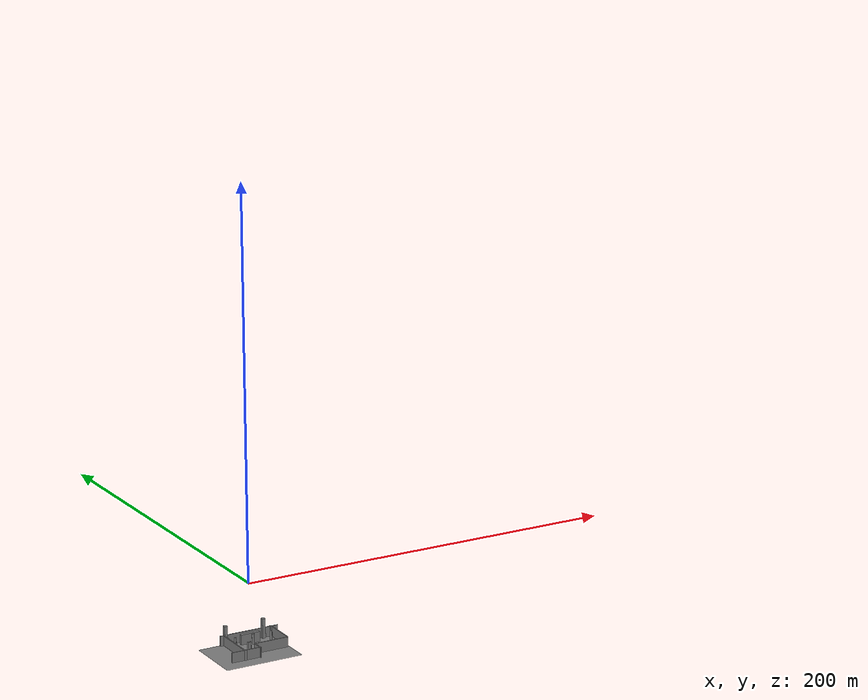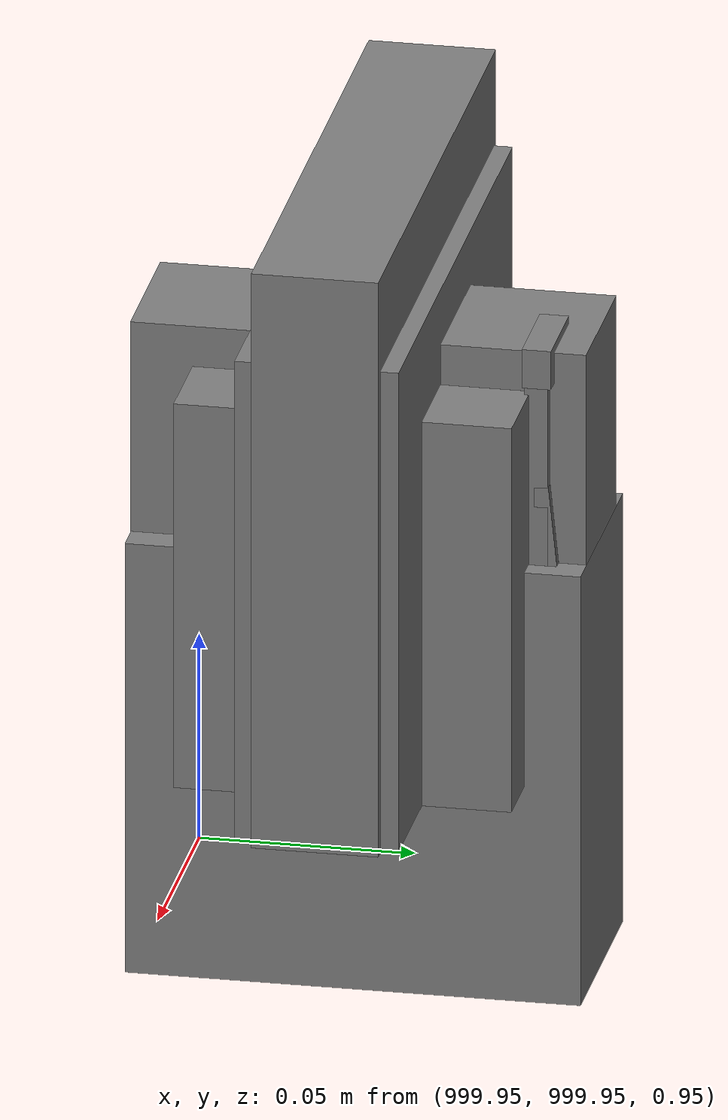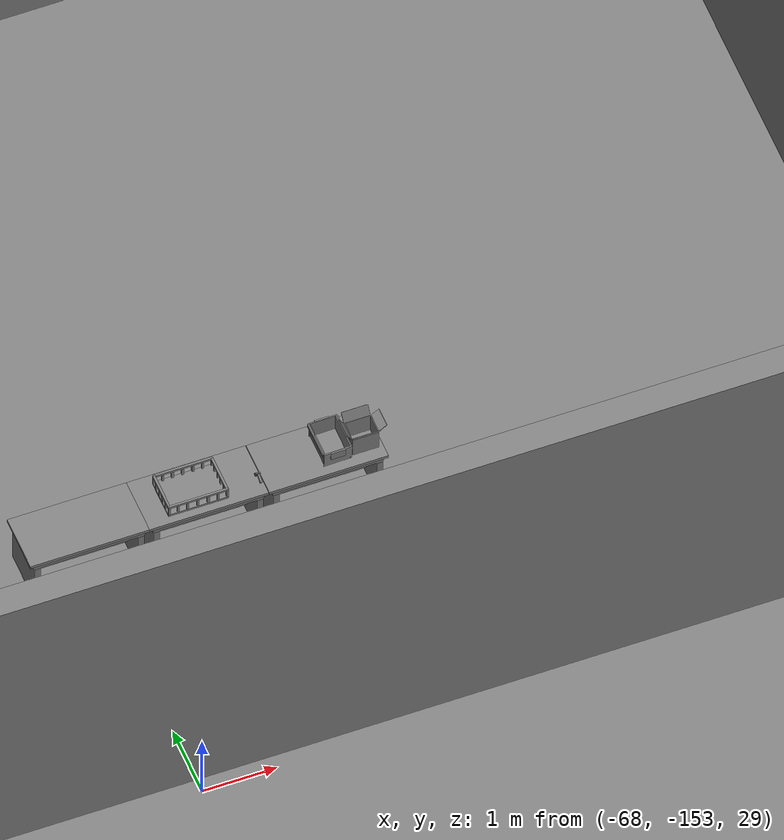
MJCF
<mujoco>
    <option gravity="0.000000000 0.000000000 -9.810000420" timestep="0.0049999999" integrator="implicitfast" density="1.225" viscosity="1.8000001e-05" noslip_iterations="10" iterations="100" sdf_iterations="50">
        <flag multiccd="disable"/>
    </option>
    <size memory="1000M"/>
    <compiler coordinate="local"/>
    <worldbody>
        <light cutoff="30" pos="0 1 1" dir="0 -1 -2"/>
        <light cutoff="30" pos="0 -1 1" dir="0 1 -2"/>
        <body pos="1000.000000000 1000.000000000 1.000000000" euler="0.000000000 0.000000000 180.000000000" name="openloong_gripper_2f85_fix_base_usda_battery_01">
            <geom contype="1" conaffinity="1" density="1000" type="box" material="" rgba="0.500000000 0.500000000 0.500000000 1.000000000" solimp="0.899999976 0.949999988 0.001000000" friction="1.000000000 0.005000000 0.000100000" solref="0.020000000 1.000000000" margin="0" condim="3" group="0" pos="-0.011123657 -0.041940309 0.101691343" quat="1.000000000 0.000000000 0.000000000 0.000000000" size="0.010800000 0.003375000 0.004725000" name="openloong_gripper_2f85_fix_base_usda_geom_94B133EC_19FF_460D_BE80_C20FE7D0648B"/>
            <geom contype="1" conaffinity="1" density="1000" type="box" material="" rgba="0.500000000 0.500000000 0.500000000 1.000000000" solimp="0.899999976 0.949999988 0.001000000" friction="1.000000000 0.005000000 0.000100000" solref="0.020000000 1.000000000" margin="0" condim="3" group="0" pos="-0.010876465 -0.044247437 0.047066893" quat="0.998702705 -0.050920475 0.000000000 0.000000000" size="0.009450001 0.002700000 0.024975000" name="openloong_gripper_2f85_fix_base_usda_geom_9C4615AE_82B8_4EC8_92CA_C24A7B5AF3D2"/>
            <geom contype="1" conaffinity="1" density="1000" type="box" material="" rgba="0.500000000 0.500000000 0.500000000 1.000000000" solimp="0.899999976 0.949999988 0.001000000" friction="1.000000000 0.005000000 0.000100000" solref="0.020000000 1.000000000" margin="0" condim="3" group="0" pos="-0.001235962 -0.000659180 0.047381196" quat="1.000000000 0.000000000 0.000000000 0.000000000" size="0.039420001 0.039150000 0.047250003" name="openloong_gripper_2f85_fix_base_usda_geom_F1869EE1_EFB7_41AC_8945_84DC95446872"/>
            <geom contype="1" conaffinity="1" density="1000" type="box" material="" rgba="0.500000000 0.500000000 0.500000000 1.000000000" solimp="0.899999976 0.949999988 0.001000000" friction="1.000000000 0.005000000 0.000100000" solref="0.020000000 1.000000000" margin="0" condim="3" group="0" pos="-0.010876465 -0.039138794 0.009851727" quat="1.000000000 0.000000000 0.000000000 0.000000000" size="0.009450001 0.010800000 0.013500000" name="openloong_gripper_2f85_fix_base_usda_geom_C5F6B03C_2051_40DD_AE04_CC09BA88B45F"/>
            <geom contype="1" conaffinity="1" density="1000" type="box" material="" rgba="0.500000000 0.500000000 0.500000000 1.000000000" solimp="0.899999976 0.949999988 0.001000000" friction="1.000000000 0.005000000 0.000100000" solref="0.020000000 1.000000000" margin="0" condim="3" group="0" pos="-0.010876465 -0.041528322 0.071508206" quat="1.000000000 0.000000000 0.000000000 0.000000000" size="0.009450001 0.002700000 0.027000001" name="openloong_gripper_2f85_fix_base_usda_geom_4A831FE4_1C2D_4A02_A543_DCA6DD18E898"/>
            <freejoint name="openloong_gripper_2f85_fix_base_usda_battery_01_joint"/>
            <site size="0.005000000 0.005000000 0.005000000" rgba="0.500000000 0.500000000 0.500000000 1.000000000" pos="0.000000000 0.000000000 0.000000000" quat="0.999961913 0.008726500 0.000000000 0.000000000" group="0" type="sphere" name="openloong_gripper_2f85_fix_base_usda_battery_01site"/>
        </body>
        <body pos="1000.000000000 1000.000000000 1.000000000" euler="0.000000000 0.000000000 180.000000000" name="openloong_gripper_2f85_fix_base_usda_wifi_box">
            <geom contype="1" conaffinity="1" density="1000" type="box" material="" rgba="0.500000000 0.500000000 0.500000000 1.000000000" solimp="0.899999976 0.949999988 0.001000000" friction="1.000000000 0.005000000 0.000100000" solref="0.020000000 1.000000000" margin="0" condim="3" group="0" pos="0.000000000 0.000000000 0.058978677" quat="0.000000000 0.000000047 0.000000000 1.000000000" size="0.068499997 0.018999999 0.059000000" name="openloong_gripper_2f85_fix_base_usda_geom_3FFF620C_DE2C_4688_9588_F0F7B7E39F24"/>
            <freejoint name="openloong_gripper_2f85_fix_base_usda_wifi_box_joint"/>
            <site size="0.005000000 0.005000000 0.005000000" rgba="0.500000000 0.500000000 0.500000000 1.000000000" pos="0.000000000 0.000000000 0.000000000" quat="0.999961913 0.008726500 0.000000000 0.000000000" group="0" type="sphere" name="openloong_gripper_2f85_fix_base_usda_wifi_boxsite"/>
        </body>
        <body pos="1000.000000000 1000.000000000 1.000000000" euler="0.000000000 0.000000000 180.000000000" name="openloong_gripper_2f85_fix_base_usda_cpu_fan">
            <geom contype="1" conaffinity="1" density="1000" type="box" material="" rgba="0.500000000 0.500000000 0.500000000 1.000000000" solimp="0.899999976 0.949999988 0.001000000" friction="1.000000000 0.005000000 0.000100000" solref="0.020000000 1.000000000" margin="0" condim="3" group="0" pos="0.000000000 0.000000000 0.070034981" quat="0.000000000 0.000000000 0.000000000 1.000000000" size="0.070700005 0.014699999 0.070700005" name="openloong_gripper_2f85_fix_base_usda_geom_9BC924FC_87AD_42B6_BA4A_DAC4C6820A8D"/>
            <freejoint name="openloong_gripper_2f85_fix_base_usda_cpu_fan_joint"/>
            <site size="0.005000000 0.005000000 0.005000000" rgba="0.500000000 0.500000000 0.500000000 1.000000000" pos="0.000000000 0.000000000 0.000000000" quat="0.999961913 0.008726535 0.000000000 0.000000000" group="0" type="sphere" name="openloong_gripper_2f85_fix_base_usda_cpu_fancsite"/>
        </body>
        <body pos="1000.000000000 1000.000000000 1.000000000" euler="0.000011953 0.000005123 -179.999984741" name="openloong_gripper_2f85_fix_base_usda_intel_box">
            <geom contype="1" conaffinity="1" density="1000" type="box" material="" rgba="0.500000000 0.500000000 0.500000000 1.000000000" solimp="0.899999976 0.949999988 0.001000000" friction="1.000000000 0.005000000 0.000100000" solref="0.020000000 1.000000000" margin="0" condim="3" group="0" pos="0.000000000 -0.000067139 0.000082284" quat="0.707106709 0.000000225 0.000000253 0.707106650" size="0.052800003 0.025300000 0.052800003" name="openloong_gripper_2f85_fix_base_usda_geom_E589303B_8C33_4C75_B6AF_6D1D032D8856"/>
            <freejoint name="openloong_gripper_2f85_fix_base_usda_intel_box_joint"/>
            <site size="0.005000000 0.005000000 0.005000000" rgba="0.500000000 0.500000000 0.500000000 1.000000000" pos="0.000000000 0.000000000 0.000000000" quat="0.999961913 0.008726500 0.000000000 0.000000000" group="0" type="sphere" name="openloong_gripper_2f85_fix_base_usda_intel_boxsite"/>
        </body>
        <body pos="-66.342063904 -149.046661377 31.162849426" euler="113.511535645 52.261505127 153.824539185" mocap="true" name="spotlight5_SpotLight"/>
        <body pos="1000.000000000 999.999938965 1.000000000" euler="0.000000000 0.000000000 180.000000000" name="openloong_gripper_2f85_fix_base_usda_intelcore_i5">
            <geom contype="1" conaffinity="1" density="1000" type="box" material="" rgba="0.500000000 0.500000000 0.500000000 1.000000000" solimp="0.899999976 0.949999988 0.001000000" friction="1.000000000 0.005000000 0.000100000" solref="0.020000000 1.000000000" margin="0" condim="3" group="0" pos="0.000000000 0.000000000 0.051722717" quat="0.707106709 0.000000000 0.000000000 -0.707106769" size="0.052800000 0.018080002 0.052800000" name="openloong_gripper_2f85_fix_base_usda_geom_CAED4E99_1917_4A58_BCE7_D8AF4C901306"/>
            <freejoint name="openloong_gripper_2f85_fix_base_usda_intelcore_i5_joint"/>
            <site size="0.005000000 0.005000000 0.005000000" rgba="0.500000000 0.500000000 0.500000000 1.000000000" pos="0.000000000 0.000000000 0.000000000" quat="0.999961913 0.008726534 0.000000000 0.000000000" group="0" type="sphere" name="openloong_gripper_2f85_fix_base_usda_intelcore_i5site"/>
        </body>
        <body pos="-66.134986877 -149.007431030 31.166290283" euler="143.638504028 89.687622070 -99.784339905" mocap="true" name="spotlight2_SpotLight"/>
        <body pos="-65.829002380 -149.400985718 31.166261673" euler="-177.369018555 -85.595886230 154.501998901" mocap="true" name="spotlight1_SpotLight"/>
        <body pos="-64.866622925 -149.383972168 30.183746338" euler="89.999984741 89.999946594 0.000000000" name="openloong_gripper_2f85_fix_base_usda_bluebox_01">
            <geom contype="1" conaffinity="1" density="1000" type="box" material="" rgba="0.500000000 0.500000000 0.500000000 1.000000000" solimp="0.899999976 0.949999988 0.001000000" friction="1.000000000 0.005000000 0.000100000" solref="0.020000000 1.000000000" margin="0" condim="3" group="0" pos="0.276580811 0.187225342 0.000068665" quat="0.707106948 0.000077471 0.707106352 0.000077486" size="0.100000001 0.057999998 0.010000000" name="openloong_gripper_2f85_fix_base_usda_geom_A43595CF_2F2A_46F1_806B_E8D09DD8A72F"/>
            <geom contype="1" conaffinity="1" density="1000" type="box" material="" rgba="0.500000000 0.500000000 0.500000000 1.000000000" solimp="0.899999976 0.949999988 0.001000000" friction="1.000000000 0.005000000 0.000100000" solref="0.020000000 1.000000000" margin="0" condim="3" group="0" pos="0.000000000 0.002883911 0.000000000" quat="0.999999881 0.000000000 0.000000000 0.000000000" size="0.254000008 0.003000000 0.172000006" name="openloong_gripper_2f85_fix_base_usda_geom_F687300C_E13A_467E_9F20_14140A425A2F"/>
            <geom contype="1" conaffinity="1" density="1000" type="box" material="" rgba="0.500000000 0.500000000 0.500000000 1.000000000" solimp="0.899999976 0.949999988 0.001000000" friction="1.000000000 0.005000000 0.000100000" solref="0.020000000 1.000000000" margin="0" condim="3" group="0" pos="0.000000000 0.124874115 0.173484802" quat="0.999796331 0.020176515 -0.000000015 0.000000030" size="0.259999990 0.119999997 0.007000000" name="openloong_gripper_2f85_fix_base_usda_geom_9284282A_4BE0_424A_9090_F2B22A17C9B7"/>
            <geom contype="1" conaffinity="1" density="1000" type="box" material="" rgba="0.500000000 0.500000000 0.500000000 1.000000000" solimp="0.899999976 0.949999988 0.001000000" friction="1.000000000 0.005000000 0.000100000" solref="0.020000000 1.000000000" margin="0" condim="3" group="0" pos="0.000000000 0.124874115 -0.173469543" quat="0.999796331 -0.020176545 -0.000000015 0.000000000" size="0.259999990 0.119999997 0.007000000" name="openloong_gripper_2f85_fix_base_usda_geom_0AA739D9_3BD4_4C5F_9601_6AEFB0514124"/>
            <geom contype="1" conaffinity="1" density="1000" type="box" material="" rgba="0.500000000 0.500000000 0.500000000 1.000000000" solimp="0.899999976 0.949999988 0.001000000" friction="1.000000000 0.005000000 0.000100000" solref="0.020000000 1.000000000" margin="0" condim="3" group="0" pos="0.000000000 0.214008331 0.188980103" quat="0.999912977 0.013176724 0.000000015 0.000000000" size="0.259999990 0.029999999 0.012500000" name="openloong_gripper_2f85_fix_base_usda_geom_ACCA9139_DDFB_4D80_95ED_DB6AF90F138B"/>
            <geom contype="1" conaffinity="1" density="1000" type="box" material="" rgba="0.500000000 0.500000000 0.500000000 1.000000000" solimp="0.899999976 0.949999988 0.001000000" friction="1.000000000 0.005000000 0.000100000" solref="0.020000000 1.000000000" margin="0" condim="3" group="0" pos="-0.258361816 0.125289917 0.001876831" quat="0.702796936 -0.020792112 0.710783124 0.020769298" size="0.189999998 0.119999997 0.009000000" name="openloong_gripper_2f85_fix_base_usda_geom_B381E45C_FED9_473E_B8B6_02C1D74A66C4"/>
            <geom contype="1" conaffinity="1" density="1000" type="box" material="" rgba="0.500000000 0.500000000 0.500000000 1.000000000" solimp="0.899999976 0.949999988 0.001000000" friction="1.000000000 0.005000000 0.000100000" solref="0.020000000 1.000000000" margin="0" condim="3" group="0" pos="0.000000000 0.214008331 -0.188980103" quat="0.999912977 -0.013176769 0.000000030 0.000000015" size="0.259999990 0.029999999 0.012500000" name="openloong_gripper_2f85_fix_base_usda_geom_F2ECEEC0_1D0F_4745_A879_1501786582D0"/>
            <geom contype="1" conaffinity="1" density="1000" type="box" material="" rgba="0.500000000 0.500000000 0.500000000 1.000000000" solimp="0.899999976 0.949999988 0.001000000" friction="1.000000000 0.005000000 0.000100000" solref="0.020000000 1.000000000" margin="0" condim="3" group="0" pos="-0.276611328 0.187225342 0.000068665" quat="0.707106650 0.000077441 0.707106709 0.000077456" size="0.100000001 0.057999998 0.010000000" name="openloong_gripper_2f85_fix_base_usda_geom_619D1375_F822_466F_A29B_C5E64CE3FDD2"/>
            <geom contype="1" conaffinity="1" density="1000" type="box" material="" rgba="0.500000000 0.500000000 0.500000000 1.000000000" solimp="0.899999976 0.949999988 0.001000000" friction="1.000000000 0.005000000 0.000100000" solref="0.020000000 1.000000000" margin="0" condim="3" group="0" pos="0.258331299 0.125289917 0.001876831" quat="0.702851415 0.018856421 0.710823774 -0.019329369" size="0.189999998 0.119999997 0.009000000" name="openloong_gripper_2f85_fix_base_usda_geom_436E468D_9759_4540_90AB_000189D72256"/>
            <freejoint name="openloong_gripper_2f85_fix_base_usda_bluebox_01_joint"/>
            <site size="0.005000000 0.005000000 0.005000000" rgba="0.500000000 0.500000000 0.500000000 1.000000000" pos="0.000000000 0.000000000 0.000000000" quat="0.999961913 0.008726534 0.000000000 0.000000000" group="0" type="sphere" name="openloong_gripper_2f85_fix_base_usda_bluebox_01site"/>
        </body>
        <body pos="-64.496299744 -149.491867065 30.235729218" euler="0.000000000 0.000000000 89.999946594" name="openloong_gripper_2f85_fix_base_usda_cardboardbox_01">
            <geom contype="1" conaffinity="1" density="1000" type="box" material="" rgba="0.500000000 0.500000000 0.500000000 1.000000000" solimp="0.899999976 0.949999988 0.001000000" friction="1.000000000 0.005000000 0.000100000" solref="0.020000000 1.000000000" margin="0" condim="3" group="0" pos="-0.003166199 -0.004086494 0.005052090" quat="1.000000000 0.000000000 0.000000000 0.000000000" size="0.142499998 0.177500010 0.005000000" name="openloong_gripper_2f85_fix_base_usda_geom_48A9BA63_D048_4AEA_BFB9_2135B7E57A5B"/>
            <geom contype="1" conaffinity="1" density="1000" type="box" material="" rgba="0.500000000 0.500000000 0.500000000 1.000000000" solimp="0.899999976 0.949999988 0.001000000" friction="1.000000000 0.005000000 0.000100000" solref="0.020000000 1.000000000" margin="0" condim="3" group="0" pos="-0.003166199 0.170316696 0.150570869" quat="1.000000000 0.000000000 0.000000000 0.000000000" size="0.142499998 0.005000000 0.149999991" name="openloong_gripper_2f85_fix_base_usda_geom_DB606ECF_FA02_417F_96DC_B284B96A1952"/>
            <geom contype="1" conaffinity="1" density="1000" type="box" material="" rgba="0.500000000 0.500000000 0.500000000 1.000000000" solimp="0.899999976 0.949999988 0.001000000" friction="1.000000000 0.005000000 0.000100000" solref="0.020000000 1.000000000" margin="0" condim="3" group="0" pos="-0.147399902 -0.005307198 0.150570869" quat="1.000000000 0.000000000 0.000000000 0.000000000" size="0.005000000 0.177500010 0.149999991" name="openloong_gripper_2f85_fix_base_usda_geom_6F66BF8E_B3B4_457D_B6C2_01258DF5B634"/>
            <geom contype="1" conaffinity="1" density="1000" type="box" material="" rgba="0.500000000 0.500000000 0.500000000 1.000000000" solimp="0.899999976 0.949999988 0.001000000" friction="1.000000000 0.005000000 0.000100000" solref="0.020000000 1.000000000" margin="0" condim="3" group="0" pos="0.140275955 -0.005307198 0.150570869" quat="1.000000000 0.000000000 0.000000000 0.000000000" size="0.005000000 0.177500010 0.149999991" name="openloong_gripper_2f85_fix_base_usda_geom_FD33482B_45B3_412B_92D6_8A4F49D8A449"/>
            <geom contype="1" conaffinity="1" density="1000" type="box" material="" rgba="0.500000000 0.500000000 0.500000000 1.000000000" solimp="0.899999976 0.949999988 0.001000000" friction="1.000000000 0.005000000 0.000100000" solref="0.020000000 1.000000000" margin="0" condim="3" group="0" pos="-0.003166199 -0.181550980 0.150570869" quat="1.000000000 0.000000000 0.000000000 0.000000000" size="0.142499998 0.005000000 0.149999991" name="openloong_gripper_2f85_fix_base_usda_geom_39F7635A_B55C_4367_A967_B4326E99415A"/>
            <freejoint name="openloong_gripper_2f85_fix_base_usda_cardboardbox_01_joint"/>
            <site size="0.005000000 0.005000000 0.005000000" rgba="0.500000000 0.500000000 0.500000000 1.000000000" pos="0.000000000 0.000000000 0.000000000" quat="0.999961913 0.008726535 0.000000000 0.000000000" group="0" type="sphere" name="openloong_gripper_2f85_fix_base_usda_site_15DAC0C3_EF86_4FA7_BF6E_7063201BA9C2"/>
            <body pos="0.139160156 -0.004048347 0.301930904" euler="-179.999954224 49.383502960 179.999954224" name="openloong_gripper_2f85_fix_base_usda_A1_006">
                <geom contype="1" conaffinity="1" density="1000" type="box" material="" rgba="0.500000000 0.500000000 0.500000000 1.000000000" solimp="0.899999976 0.949999988 0.001000000" friction="1.000000000 0.005000000 0.000100000" solref="0.020000000 1.000000000" margin="0" condim="3" group="0" pos="-0.071587563 0.000009537 0.001745224" quat="0.999999881 0.000000000 0.000000000 0.000000000" size="0.071249999 0.179999992 0.002500000" name="openloong_gripper_2f85_fix_base_usda_geom_51FCD30A_AE4F_4CBA_98B7_DE38792459F6"/>
                <joint armature="0" stiffness="0.07" damping="0.0099999998" axis="0.000000 1.000000 0.000000" type="hinge" name="openloong_gripper_2f85_fix_base_usda_A1_006"/>
            </body>
            <body pos="-0.145902634 -0.004086494 0.301938057" euler="-180.000000000 -60.000011444 -180.000000000" name="openloong_gripper_2f85_fix_base_usda_A2_006">
                <geom contype="1" conaffinity="1" density="1000" type="box" material="" rgba="0.500000000 0.500000000 0.500000000 1.000000000" solimp="0.899999976 0.949999988 0.001000000" friction="1.000000000 0.005000000 0.000100000" solref="0.020000000 1.000000000" margin="0" condim="3" group="0" pos="0.071268082 0.000009537 0.002717972" quat="0.000002921 0.000000000 -0.000000030 0.999999881" size="0.071249999 0.179999992 0.002500000" name="openloong_gripper_2f85_fix_base_usda_geom_1F7ACDE2_8E33_4706_8FF5_1388099CEC43"/>
                <joint armature="0" stiffness="0.07" damping="0.0099999998" axis="0.000000 1.000000 0.000000" type="hinge" name="openloong_gripper_2f85_fix_base_usda_A2_006"/>
            </body>
            <body pos="-0.003385544 0.175991058 0.301930904" euler="-125.858116150 -0.000004561 0.000002331" name="openloong_gripper_2f85_fix_base_usda_B2_006">
                <geom contype="1" conaffinity="1" density="1000" type="box" material="" rgba="0.500000000 0.500000000 0.500000000 1.000000000" solimp="0.899999976 0.949999988 0.001000000" friction="1.000000000 0.005000000 0.000100000" solref="0.020000000 1.000000000" margin="0" condim="3" group="0" pos="0.000009537 -0.070939064 -0.002470016" quat="0.999614120 0.027776197 -0.000000015 0.000000030" size="0.137500003 0.064999998 0.005000000" name="openloong_gripper_2f85_fix_base_usda_geom_CDDD990B_75D9_4F7F_B92A_3E63525670DD"/>
                <joint armature="0" stiffness="0.07" damping="0.0099999998" axis="1.000000 0.000000 0.000000" type="hinge" name="openloong_gripper_2f85_fix_base_usda_B2_006"/>
            </body>
            <body pos="-0.003385544 -0.184140205 0.301938057" euler="147.805557251 0.000000000 0.000000000" name="openloong_gripper_2f85_fix_base_usda_B1_006">
                <geom contype="1" conaffinity="1" density="1000" type="box" material="" rgba="0.500000000 0.500000000 0.500000000 1.000000000" solimp="0.899999976 0.949999988 0.001000000" friction="1.000000000 0.005000000 0.000100000" solref="0.020000000 1.000000000" margin="0" condim="3" group="0" pos="-0.000028610 0.070202351 -0.002703667" quat="0.999614179 -0.027776167 0.000000000 0.000000000" size="0.137500003 0.064999998 0.005000000" name="openloong_gripper_2f85_fix_base_usda_geom_55C9E4BE_A0FA_4F8C_9AAF_13A6F1A722D1"/>
                <joint armature="0" stiffness="0.07" damping="0.0099999998" axis="1.000000 0.000000 0.000000" type="hinge" name="openloong_gripper_2f85_fix_base_usda_B1_006"/>
            </body>
        </body>
        <body pos="-65.882858276 -149.481979370 30.229999542" euler="-64.487716675 0.000000000 0.000000000" name="openloong_gripper_2f85_fix_base_usda_Barcode">
            <geom contype="1" conaffinity="1" density="1000" type="box" material="" rgba="0.500000000 0.500000000 0.500000000 1.000000000" solimp="0.899999976 0.949999988 0.001000000" friction="1.000000000 0.005000000 0.000100000" solref="0.020000000 1.000000000" margin="0" condim="3" group="0" pos="0.000000000 0.013038635 0.001419067" quat="0.000000000 0.000000000 0.000000000 1.000000119" size="0.034000002 0.010000000 0.017999999" name="openloong_gripper_2f85_fix_base_usda_geom_23B03395_3FDC_4B89_9ED7_5EE84F9B3B50"/>
            <geom contype="1" conaffinity="1" density="1000" type="box" material="" rgba="0.500000000 0.500000000 0.500000000 1.000000000" solimp="0.899999976 0.949999988 0.001000000" friction="1.000000000 0.005000000 0.000100000" solref="0.020000000 1.000000000" margin="0" condim="3" group="0" pos="0.000000000 -0.035301208 -0.007095337" quat="0.000000000 0.000000000 -0.043619365 0.999048233" size="0.028999999 0.010000000 0.020000000" name="openloong_gripper_2f85_fix_base_usda_geom_E811FEE5_7B37_49F8_998E_1A8EE1A9D8D6"/>
            <geom contype="1" conaffinity="1" density="1000" type="box" material="" rgba="0.500000000 0.500000000 0.500000000 1.000000000" solimp="0.899999976 0.949999988 0.001000000" friction="1.000000000 0.005000000 0.000100000" solref="0.020000000 1.000000000" margin="0" condim="3" group="0" pos="0.000000000 -0.043411255 -0.011749268" quat="0.922262907 0.386563420 0.000000000 0.000000000" size="0.026000001 0.010000000 0.020000000" name="openloong_gripper_2f85_fix_base_usda_geom_0B26A7F8_81CA_4AFC_AD44_A0548CA03B6C"/>
            <geom contype="1" conaffinity="1" density="1000" type="box" material="" rgba="0.500000000 0.500000000 0.500000000 1.000000000" solimp="0.899999976 0.949999988 0.001000000" friction="1.000000000 0.005000000 0.000100000" solref="0.020000000 1.000000000" margin="0" condim="3" group="0" pos="0.000000000 -0.016967773 -0.031860352" quat="0.000000000 0.000000000 0.000000000 1.000000119" size="0.008000000 0.010000000 0.013000000" name="openloong_gripper_2f85_fix_base_usda_geom_A9C20F89_A95A_4D37_BED0_D70A9FFC7D2C"/>
            <geom contype="1" conaffinity="1" density="1000" type="box" material="" rgba="0.500000000 0.500000000 0.500000000 1.000000000" solimp="0.899999976 0.949999988 0.001000000" friction="1.000000000 0.005000000 0.000100000" solref="0.020000000 1.000000000" margin="0" condim="3" group="0" pos="0.000000000 -0.001869202 0.000312805" quat="0.953716993 0.300705761 0.000000000 0.000000000" size="0.032000002 0.010000000 0.018999999" name="openloong_gripper_2f85_fix_base_usda_geom_17E0E9E9_7924_43A0_A464_0EA1241D3A8E"/>
            <geom contype="1" conaffinity="1" density="1000" type="box" material="" rgba="0.500000000 0.500000000 0.500000000 1.000000000" solimp="0.899999976 0.949999988 0.001000000" friction="1.000000000 0.005000000 0.000100000" solref="0.020000000 1.000000000" margin="0" condim="3" group="0" pos="0.000000000 -0.019531250 -0.003173828" quat="0.953716993 0.300705761 0.000000000 0.000000000" size="0.030999999 0.010000000 0.020000000" name="openloong_gripper_2f85_fix_base_usda_geom_55318C02_5546_4A1E_80E6_EE78E5F8FFBA"/>
            <geom contype="1" conaffinity="1" density="1000" type="box" material="" rgba="0.500000000 0.500000000 0.500000000 1.000000000" solimp="0.899999976 0.949999988 0.001000000" friction="1.000000000 0.005000000 0.000100000" solref="0.020000000 1.000000000" margin="0" condim="3" group="0" pos="0.000000000 -0.035301208 -0.007095337" quat="0.953716993 0.300705761 0.000000000 0.000000000" size="0.028999999 0.010000000 0.020000000" name="openloong_gripper_2f85_fix_base_usda_geom_837F0D01_DFAE_491D_AE7D_D49A1D397EA0"/>
            <geom contype="1" conaffinity="1" density="1000" type="box" material="" rgba="0.500000000 0.500000000 0.500000000 1.000000000" solimp="0.899999976 0.949999988 0.001000000" friction="1.000000000 0.005000000 0.000100000" solref="0.020000000 1.000000000" margin="0" condim="3" group="0" pos="0.000000000 -0.042617798 -0.071121216" quat="0.000000000 0.000000000 0.000000000 1.000000119" size="0.013000000 0.021000000 0.059999999" name="openloong_gripper_2f85_fix_base_usda_geom_81B4613F_1002_4093_8585_8323A1501F41"/>
            <freejoint name="openloong_gripper_2f85_fix_base_usda_Barcode_joint"/>
            <site size="0.005000000 0.005000000 0.005000000" rgba="0.500000000 0.500000000 0.500000000 1.000000000" pos="0.000000000 0.000000000 0.000000000" quat="1.000000000 0.000000000 0.000000000 0.000000000" group="0" type="sphere" name="openloong_gripper_2f85_fix_base_usda_Barcode_site"/>
        </body>
        <body pos="-66.745018005 -149.392349243 30.184000015" euler="0.000000000 0.000000000 89.999946594" name="[22329804331601]_Basket_01">
            <geom contype="1" conaffinity="1" density="1000" type="box" material="" rgba="0.500000000 0.500000000 0.500000000 1.000000000" solimp="0.899999976 0.949999988 0.001000000" friction="1.000000000 0.005000000 0.000100000" solref="0.020000000 1.000000000" margin="0" condim="3" group="0" pos="-0.052425385 0.389207840 0.089787483" quat="0.707107008 0.000000000 0.000000000 0.707106411" size="0.014249999 0.014249999 0.059999999" name="[22329804331601]_geom_7FA56946_4BAC_4F22_953D_4B563231ECCC"/>
            <geom contype="1" conaffinity="1" density="1000" type="box" material="" rgba="0.500000000 0.500000000 0.500000000 1.000000000" solimp="0.899999976 0.949999988 0.001000000" friction="1.000000000 0.005000000 0.000100000" solref="0.020000000 1.000000000" margin="0" condim="3" group="0" pos="0.264015198 -0.133043289 0.089787483" quat="0.707107008 0.000000000 0.000000000 0.707106411" size="0.014249999 0.014249999 0.059999999" name="[22329804331601]_geom_9D342C01_C8A0_448D_838F_8017DE896E48"/>
            <geom contype="1" conaffinity="1" density="1000" type="box" material="" rgba="0.500000000 0.500000000 0.500000000 1.000000000" solimp="0.899999976 0.949999988 0.001000000" friction="1.000000000 0.005000000 0.000100000" solref="0.020000000 1.000000000" margin="0" condim="3" group="0" pos="-0.264015198 -0.265548706 0.089793205" quat="0.707107008 0.000000000 0.000000000 0.707106411" size="0.014249999 0.014249999 0.059999999" name="[22329804331601]_geom_88D50CE0_EB13_491E_94FF_038F189C51B0"/>
            <geom contype="1" conaffinity="1" density="1000" type="box" material="" rgba="0.500000000 0.500000000 0.500000000 1.000000000" solimp="0.899999976 0.949999988 0.001000000" friction="1.000000000 0.005000000 0.000100000" solref="0.020000000 1.000000000" margin="0" condim="3" group="0" pos="-0.160263062 -0.389322281 0.089793205" quat="0.707107008 0.000000000 0.000000000 0.707106411" size="0.014249999 0.014249999 0.059999999" name="[22329804331601]_geom_ED7BF228_D11B_4A64_B211_28B098D31200"/>
            <geom contype="1" conaffinity="1" density="1000" type="box" material="" rgba="0.500000000 0.500000000 0.500000000 1.000000000" solimp="0.899999976 0.949999988 0.001000000" friction="1.000000000 0.005000000 0.000100000" solref="0.020000000 1.000000000" margin="0" condim="3" group="0" pos="0.162265778 -0.389322281 0.089787483" quat="0.707107008 0.000000000 0.000000000 0.707106411" size="0.014249999 0.014249999 0.059999999" name="[22329804331601]_geom_2A2203C9_D304_4AD8_B39A_0DD5D850D1A2"/>
            <geom contype="1" conaffinity="1" density="1000" type="box" material="" rgba="0.500000000 0.500000000 0.500000000 1.000000000" solimp="0.899999976 0.949999988 0.001000000" friction="1.000000000 0.005000000 0.000100000" solref="0.020000000 1.000000000" margin="0" condim="3" group="0" pos="0.264015198 0.389207840 0.089787483" quat="0.707107008 0.000000000 0.000000000 0.707106411" size="0.014249999 0.014249999 0.059999999" name="[22329804331601]_geom_AD5ACF99_DFCD_47F6_861D_E0890B1C0E9C"/>
            <geom contype="1" conaffinity="1" density="1000" type="box" material="" rgba="0.500000000 0.500000000 0.500000000 1.000000000" solimp="0.899999976 0.949999988 0.001000000" friction="1.000000000 0.005000000 0.000100000" solref="0.020000000 1.000000000" margin="0" condim="3" group="0" pos="-0.264015198 -0.133043289 0.089793205" quat="0.707107008 0.000000000 0.000000000 0.707106411" size="0.014249999 0.014249999 0.059999999" name="[22329804331601]_geom_0C2FF278_BFB4_44CE_86C3_46E4FA47DEBD"/>
            <geom contype="1" conaffinity="1" density="1000" type="box" material="" rgba="0.500000000 0.500000000 0.500000000 1.000000000" solimp="0.899999976 0.949999988 0.001000000" friction="1.000000000 0.005000000 0.000100000" solref="0.020000000 1.000000000" margin="0" condim="3" group="0" pos="-0.264026642 0.269256592 0.089793205" quat="0.707107008 0.000000000 0.000000000 0.707106411" size="0.014249999 0.014249999 0.059999999" name="[22329804331601]_geom_897F1086_DF1B_4238_A835_597ADAF54AE3"/>
            <geom contype="1" conaffinity="1" density="1000" type="box" material="" rgba="0.500000000 0.500000000 0.500000000 1.000000000" solimp="0.899999976 0.949999988 0.001000000" friction="1.000000000 0.005000000 0.000100000" solref="0.020000000 1.000000000" margin="0" condim="3" group="0" pos="0.054462433 0.389207840 0.089787483" quat="0.707107008 0.000000000 0.000000000 0.707106411" size="0.014249999 0.014249999 0.059999999" name="[22329804331601]_geom_BA9B1096_0C8B_41EF_A596_7DE9FC97E642"/>
            <geom contype="1" conaffinity="1" density="1000" type="box" material="" rgba="0.500000000 0.500000000 0.500000000 1.000000000" solimp="0.899999976 0.949999988 0.001000000" friction="1.000000000 0.005000000 0.000100000" solref="0.020000000 1.000000000" margin="0" condim="3" group="0" pos="0.054462433 -0.389322281 0.089787483" quat="0.707107008 0.000000000 0.000000000 0.707106411" size="0.014249999 0.014249999 0.059999999" name="[22329804331601]_geom_BD422D21_172C_4BB1_807F_01444C0D7331"/>
            <geom contype="1" conaffinity="1" density="1000" type="box" material="" rgba="0.500000000 0.500000000 0.500000000 1.000000000" solimp="0.899999976 0.949999988 0.001000000" friction="1.000000000 0.005000000 0.000100000" solref="0.020000000 1.000000000" margin="0" condim="3" group="0" pos="0.264015198 0.269256592 0.089793205" quat="0.707107008 0.000000000 0.000000000 0.707106411" size="0.014249999 0.014249999 0.059999999" name="[22329804331601]_geom_43B0B6D6_A7EC_4B03_A2EC_CBA2C6DE96AF"/>
            <geom contype="1" conaffinity="1" density="1000" type="box" material="" rgba="0.500000000 0.500000000 0.500000000 1.000000000" solimp="0.899999976 0.949999988 0.001000000" friction="1.000000000 0.005000000 0.000100000" solref="0.020000000 1.000000000" margin="0" condim="3" group="0" pos="0.264015198 -0.389322281 0.089787483" quat="0.707107008 0.000000000 0.000000000 0.707106411" size="0.014249999 0.014249999 0.059999999" name="[22329804331601]_geom_A074AD24_1F4C_4CD8_A4C7_65A2E27EFE4D"/>
            <geom contype="1" conaffinity="1" density="1000" type="box" material="" rgba="0.500000000 0.500000000 0.500000000 1.000000000" solimp="0.899999976 0.949999988 0.001000000" friction="1.000000000 0.005000000 0.000100000" solref="0.020000000 1.000000000" margin="0" condim="3" group="0" pos="0.000000000 0.000000000 0.015998840" quat="0.707107008 0.000000000 0.000000000 0.707106411" size="0.403499991 0.279000014 0.015750000" name="[22329804331601]_geom_81DCABB0_873F_41FB_A2DB_0D39C56A46AC"/>
            <geom contype="1" conaffinity="1" density="1000" type="box" material="" rgba="0.500000000 0.500000000 0.500000000 1.000000000" solimp="0.899999976 0.949999988 0.001000000" friction="1.000000000 0.005000000 0.000100000" solref="0.020000000 1.000000000" margin="0" condim="3" group="0" pos="0.000000000 -0.389476776 0.163619041" quat="0.707107008 0.000000000 0.000000000 0.707106411" size="0.015000000 0.277500004 0.015750000" name="[22329804331601]_geom_2F2D445F_2749_46C6_925C_917164592F07"/>
            <geom contype="1" conaffinity="1" density="1000" type="box" material="" rgba="0.500000000 0.500000000 0.500000000 1.000000000" solimp="0.899999976 0.949999988 0.001000000" friction="1.000000000 0.005000000 0.000100000" solref="0.020000000 1.000000000" margin="0" condim="3" group="0" pos="0.162265778 0.389207840 0.089787483" quat="0.707107008 0.000000000 0.000000000 0.707106411" size="0.014249999 0.014249999 0.059999999" name="[22329804331601]_geom_DDFB58C1_8888_488C_A84C_06A86415791D"/>
            <geom contype="1" conaffinity="1" density="1000" type="box" material="" rgba="0.500000000 0.500000000 0.500000000 1.000000000" solimp="0.899999976 0.949999988 0.001000000" friction="1.000000000 0.005000000 0.000100000" solref="0.020000000 1.000000000" margin="0" condim="3" group="0" pos="0.000000000 0.389471054 0.163619041" quat="0.707107008 0.000000000 0.000000000 0.707106411" size="0.015000000 0.277500004 0.015750000" name="[22329804331601]_geom_0507EDC0_4E2A_4DC7_AB42_26477F1DA427"/>
            <geom contype="1" conaffinity="1" density="1000" type="box" material="" rgba="0.500000000 0.500000000 0.500000000 1.000000000" solimp="0.899999976 0.949999988 0.001000000" friction="1.000000000 0.005000000 0.000100000" solref="0.020000000 1.000000000" margin="0" condim="3" group="0" pos="-0.263511658 0.000000000 0.163619041" quat="0.707107008 0.000000000 0.000000000 0.707106411" size="0.403499991 0.015000000 0.015750000" name="[22329804331601]_geom_50A1BA05_1C60_4844_BED7_84D75A7EC570"/>
            <geom contype="1" conaffinity="1" density="1000" type="box" material="" rgba="0.500000000 0.500000000 0.500000000 1.000000000" solimp="0.899999976 0.949999988 0.001000000" friction="1.000000000 0.005000000 0.000100000" solref="0.020000000 1.000000000" margin="0" condim="3" group="0" pos="-0.264015198 0.141334534 0.089793205" quat="0.707107008 0.000000000 0.000000000 0.707106411" size="0.014249999 0.014249999 0.059999999" name="[22329804331601]_geom_45DAE0D8_2AB5_42C5_94D8_AC08F12C1623"/>
            <geom contype="1" conaffinity="1" density="1000" type="box" material="" rgba="0.500000000 0.500000000 0.500000000 1.000000000" solimp="0.899999976 0.949999988 0.001000000" friction="1.000000000 0.005000000 0.000100000" solref="0.020000000 1.000000000" margin="0" condim="3" group="0" pos="0.264015198 -0.265548706 0.089787483" quat="0.707107008 0.000000000 0.000000000 0.707106411" size="0.014249999 0.014249999 0.059999999" name="[22329804331601]_geom_5EB4CEF5_841E_473B_88D6_FF695A47C848"/>
            <geom contype="1" conaffinity="1" density="1000" type="box" material="" rgba="0.500000000 0.500000000 0.500000000 1.000000000" solimp="0.899999976 0.949999988 0.001000000" friction="1.000000000 0.005000000 0.000100000" solref="0.020000000 1.000000000" margin="0" condim="3" group="0" pos="-0.160263062 0.389207840 0.089787483" quat="0.707107008 0.000000000 0.000000000 0.707106411" size="0.014249999 0.014249999 0.059999999" name="[22329804331601]_geom_78EC4FAC_DEC0_44C0_B0EA_01E815259A86"/>
            <geom contype="1" conaffinity="1" density="1000" type="box" material="" rgba="0.500000000 0.500000000 0.500000000 1.000000000" solimp="0.899999976 0.949999988 0.001000000" friction="1.000000000 0.005000000 0.000100000" solref="0.020000000 1.000000000" margin="0" condim="3" group="0" pos="-0.052425385 -0.389322281 0.089787483" quat="0.707107008 0.000000000 0.000000000 0.707106411" size="0.014249999 0.014249999 0.059999999" name="[22329804331601]_geom_70E3F501_DF95_4C3C_BAC1_513A1A8D4E8E"/>
            <geom contype="1" conaffinity="1" density="1000" type="box" material="" rgba="0.500000000 0.500000000 0.500000000 1.000000000" solimp="0.899999976 0.949999988 0.001000000" friction="1.000000000 0.005000000 0.000100000" solref="0.020000000 1.000000000" margin="0" condim="3" group="0" pos="-0.264026642 -0.389322281 0.089793205" quat="0.707107008 0.000000000 0.000000000 0.707106411" size="0.014249999 0.014249999 0.059999999" name="[22329804331601]_geom_F4D5020E_1C7E_4A9A_A4A0_6CCA82FCCD3F"/>
            <geom contype="1" conaffinity="1" density="1000" type="box" material="" rgba="0.500000000 0.500000000 0.500000000 1.000000000" solimp="0.899999976 0.949999988 0.001000000" friction="1.000000000 0.005000000 0.000100000" solref="0.020000000 1.000000000" margin="0" condim="3" group="0" pos="0.264015198 0.141334534 0.089787483" quat="0.707107008 0.000000000 0.000000000 0.707106411" size="0.014249999 0.014249999 0.059999999" name="[22329804331601]_geom_D4D80F27_4383_4F7D_BA53_64F91B9F48C0"/>
            <geom contype="1" conaffinity="1" density="1000" type="box" material="" rgba="0.500000000 0.500000000 0.500000000 1.000000000" solimp="0.899999976 0.949999988 0.001000000" friction="1.000000000 0.005000000 0.000100000" solref="0.020000000 1.000000000" margin="0" condim="3" group="0" pos="-0.264015198 0.389207840 0.089793205" quat="0.707107008 0.000000000 0.000000000 0.707106411" size="0.014249999 0.014249999 0.059999999" name="[22329804331601]_geom_7136580D_B667_4C77_B12F_C595D2C52D66"/>
            <geom contype="1" conaffinity="1" density="1000" type="box" material="" rgba="0.500000000 0.500000000 0.500000000 1.000000000" solimp="0.899999976 0.949999988 0.001000000" friction="1.000000000 0.005000000 0.000100000" solref="0.020000000 1.000000000" margin="0" condim="3" group="0" pos="0.264015198 0.004480362 0.089787483" quat="0.707107008 0.000000000 0.000000000 0.707106411" size="0.014249999 0.014249999 0.059999999" name="[22329804331601]_geom_B6899BB9_E568_4D12_9768_8D73DF523739"/>
            <geom contype="1" conaffinity="1" density="1000" type="box" material="" rgba="0.500000000 0.500000000 0.500000000 1.000000000" solimp="0.899999976 0.949999988 0.001000000" friction="1.000000000 0.005000000 0.000100000" solref="0.020000000 1.000000000" margin="0" condim="3" group="0" pos="0.263694763 -0.000011444 0.163619041" quat="0.707107008 0.000000000 0.000000000 0.707106411" size="0.403499991 0.015000000 0.015750000" name="[22329804331601]_geom_168A7F9F_B485_4DB1_839A_7B38FDD65F37"/>
            <geom contype="1" conaffinity="1" density="1000" type="box" material="" rgba="0.500000000 0.500000000 0.500000000 1.000000000" solimp="0.899999976 0.949999988 0.001000000" friction="1.000000000 0.005000000 0.000100000" solref="0.020000000 1.000000000" margin="0" condim="3" group="0" pos="-0.264015198 0.004480362 0.089793205" quat="0.707107008 0.000000000 0.000000000 0.707106411" size="0.014249999 0.014249999 0.059999999" name="[22329804331601]_geom_B82FEE87_1F87_4E7C_9B1E_5AE365A084F5"/>
            <freejoint name="[22329804331601]_joint_E13B036D_558B_4142_BA4F_599A94D992CA"/>
        </body>
        <body pos="0.000000000 0.000000000 0.000000000" euler="0.000000000 0.000000000 0.000000000" name="Static Objects_Static Objects">
            <geom contype="1" conaffinity="1" density="1000" type="box" material="" rgba="0.500000000 0.500000000 0.500000000 1.000000000" solimp="0.899999976 0.949999988 0.001000000" friction="1.000000000 0.005000000 0.000100000" solref="0.020000000 1.000000000" margin="0" condim="3" group="0" pos="-67.544113159 -149.365814209 29.727830887" quat="0.500000417 0.499999970 0.499999553 0.499999970" size="0.381000012 0.319999993 0.041000001" name="Static Objects_geom_8302911B_1472_4EF3_BF3F_DBDF002DD481"/>
            <geom contype="1" conaffinity="1" density="1000" type="box" material="" rgba="0.500000000 0.500000000 0.500000000 1.000000000" solimp="0.899999976 0.949999988 0.001000000" friction="1.000000000 0.005000000 0.000100000" solref="0.020000000 1.000000000" margin="0" condim="3" group="0" pos="-68.239501953 -149.365814209 30.086868286" quat="0.500000417 0.499999970 0.499999553 0.499999970" size="0.370999992 0.039500002 0.745000005" name="Static Objects_geom_C25E6C3C_E1DD_4F88_AA4F_C51ED78968BF"/>
            <geom contype="1" conaffinity="1" density="1000" type="box" material="" rgba="0.500000000 0.500000000 0.500000000 1.000000000" solimp="0.899999976 0.949999988 0.001000000" friction="1.000000000 0.005000000 0.000100000" solref="0.020000000 1.000000000" margin="0" condim="3" group="0" pos="-68.239501953 -149.365814209 30.147235870" quat="0.500000417 0.499999970 0.499999553 0.499999970" size="0.400000006 0.022000000 0.800000012" name="Static Objects_geom_480A1AE0_2351_46D5_B168_3FEEDC286AF3"/>
            <geom contype="1" conaffinity="1" density="1000" type="box" material="" rgba="0.500000000 0.500000000 0.500000000 1.000000000" solimp="0.899999976 0.949999988 0.001000000" friction="1.000000000 0.005000000 0.000100000" solref="0.020000000 1.000000000" margin="0" condim="3" group="0" pos="-68.934890747 -149.365814209 29.727830887" quat="0.500000417 0.499999970 0.499999553 0.499999970" size="0.381000012 0.319999993 0.041000001" name="Static Objects_geom_D8105EEC_2642_4F32_B924_9E7533D43B60"/>
            <geom contype="1" conaffinity="1" density="1000" type="box" material="" rgba="0.500000000 0.500000000 0.500000000 1.000000000" solimp="0.899999976 0.949999988 0.001000000" friction="1.000000000 0.005000000 0.000100000" solref="0.020000000 1.000000000" margin="0" condim="3" group="0" pos="-68.239501953 -149.365814209 29.561563492" quat="0.500000417 0.499999970 0.499999553 0.499999970" size="0.020000000 0.022000000 0.660000026" name="Static Objects_geom_C7868BDF_8915_4386_A1C8_E56F7DCA5151"/>
            <geom contype="1" conaffinity="1" density="1000" type="box" material="" rgba="0.500000000 0.500000000 0.500000000 1.000000000" solimp="0.899999976 0.949999988 0.001000000" friction="1.000000000 0.005000000 0.000100000" solref="0.020000000 1.000000000" margin="0" condim="3" group="0" pos="-65.945671082 -149.365814209 29.727830887" quat="0.500000417 0.499999970 0.499999553 0.499999970" size="0.381000012 0.319999993 0.041000001" name="Static Objects_geom_145D702E_FD65_402A_96DB_142CE8A21377"/>
            <geom contype="1" conaffinity="1" density="1000" type="box" material="" rgba="0.500000000 0.500000000 0.500000000 1.000000000" solimp="0.899999976 0.949999988 0.001000000" friction="1.000000000 0.005000000 0.000100000" solref="0.020000000 1.000000000" margin="0" condim="3" group="0" pos="-66.641059875 -149.365814209 30.086868286" quat="0.500000417 0.499999970 0.499999553 0.499999970" size="0.370999992 0.039500002 0.745000005" name="Static Objects_geom_F89025E3_B713_4F3C_AD60_43FEBC4E8CCC"/>
            <geom contype="1" conaffinity="1" density="1000" type="box" material="" rgba="0.500000000 0.500000000 0.500000000 1.000000000" solimp="0.899999976 0.949999988 0.001000000" friction="1.000000000 0.005000000 0.000100000" solref="0.020000000 1.000000000" margin="0" condim="3" group="0" pos="-66.641059875 -149.365814209 30.147235870" quat="0.500000417 0.499999970 0.499999553 0.499999970" size="0.400000006 0.022000000 0.800000012" name="Static Objects_geom_2622C721_D87B_4F39_A42E_031A572D7B1F"/>
            <geom contype="1" conaffinity="1" density="1000" type="box" material="" rgba="0.500000000 0.500000000 0.500000000 1.000000000" solimp="0.899999976 0.949999988 0.001000000" friction="1.000000000 0.005000000 0.000100000" solref="0.020000000 1.000000000" margin="0" condim="3" group="0" pos="-67.336448669 -149.365814209 29.727830887" quat="0.500000417 0.499999970 0.499999553 0.499999970" size="0.381000012 0.319999993 0.041000001" name="Static Objects_geom_FC7BDC68_A230_4F43_90AE_F321CDBBAE49"/>
            <geom contype="1" conaffinity="1" density="1000" type="box" material="" rgba="0.500000000 0.500000000 0.500000000 1.000000000" solimp="0.899999976 0.949999988 0.001000000" friction="1.000000000 0.005000000 0.000100000" solref="0.020000000 1.000000000" margin="0" condim="3" group="0" pos="-66.641059875 -149.365814209 29.561563492" quat="0.500000417 0.499999970 0.499999553 0.499999970" size="0.020000000 0.022000000 0.660000026" name="Static Objects_geom_CD00F757_CBAB_42E7_99F2_DCE95C3B8953"/>
            <geom contype="1" conaffinity="1" density="1000" type="box" material="" rgba="0.500000000 0.500000000 0.500000000 1.000000000" solimp="0.899999976 0.949999988 0.001000000" friction="1.000000000 0.005000000 0.000100000" solref="0.020000000 1.000000000" margin="0" condim="3" group="0" pos="-64.338577271 -149.365814209 29.727830887" quat="0.500000417 0.499999970 0.499999553 0.499999970" size="0.381000012 0.319999993 0.041000001" name="Static Objects_geom_59DF7FA2_02E0_4EFF_94AD_82DA120F4836"/>
            <geom contype="1" conaffinity="1" density="1000" type="box" material="" rgba="0.500000000 0.500000000 0.500000000 1.000000000" solimp="0.899999976 0.949999988 0.001000000" friction="1.000000000 0.005000000 0.000100000" solref="0.020000000 1.000000000" margin="0" condim="3" group="0" pos="-65.033966064 -149.365814209 30.086868286" quat="0.500000417 0.499999970 0.499999553 0.499999970" size="0.370999992 0.039500002 0.745000005" name="Static Objects_geom_076A355B_DC3A_459F_B10F_08CB9A26C96A"/>
            <geom contype="1" conaffinity="1" density="1000" type="box" material="" rgba="0.500000000 0.500000000 0.500000000 1.000000000" solimp="0.899999976 0.949999988 0.001000000" friction="1.000000000 0.005000000 0.000100000" solref="0.020000000 1.000000000" margin="0" condim="3" group="0" pos="-65.033966064 -149.365814209 30.147235870" quat="0.500000417 0.499999970 0.499999553 0.499999970" size="0.400000006 0.022000000 0.800000012" name="Static Objects_geom_CBD56F91_8F26_462C_BAB4_E0FCF1DC5A55"/>
            <geom contype="1" conaffinity="1" density="1000" type="box" material="" rgba="0.500000000 0.500000000 0.500000000 1.000000000" solimp="0.899999976 0.949999988 0.001000000" friction="1.000000000 0.005000000 0.000100000" solref="0.020000000 1.000000000" margin="0" condim="3" group="0" pos="-65.729354858 -149.365814209 29.727830887" quat="0.500000417 0.499999970 0.499999553 0.499999970" size="0.381000012 0.319999993 0.041000001" name="Static Objects_geom_F789F2B2_1786_4340_AED3_03BB5010A51F"/>
            <geom contype="1" conaffinity="1" density="1000" type="box" material="" rgba="0.500000000 0.500000000 0.500000000 1.000000000" solimp="0.899999976 0.949999988 0.001000000" friction="1.000000000 0.005000000 0.000100000" solref="0.020000000 1.000000000" margin="0" condim="3" group="0" pos="-65.033966064 -149.365814209 29.561563492" quat="0.500000417 0.499999970 0.499999553 0.499999970" size="0.020000000 0.022000000 0.660000026" name="Static Objects_geom_17B25E7A_A46B_4407_A44B_A1F117B539B6"/>
            <geom contype="1" conaffinity="1" density="1000" type="box" material="" rgba="0.500000000 0.500000000 0.500000000 1.000000000" solimp="0.899999976 0.949999988 0.001000000" friction="1.000000000 0.005000000 0.000100000" solref="0.020000000 1.000000000" margin="0" condim="3" group="0" pos="-61.754566193 -137.853729248 33.906845093" quat="0.707107067 0.000000000 0.000000000 0.707106471" size="0.759999990 0.759999990 4.500000000" name="Static Objects_geom_DE9D5063_69A8_4F56_9A84_CB263B163572"/>
            <geom contype="1" conaffinity="1" density="1000" type="box" material="" rgba="0.500000000 0.500000000 0.500000000 1.000000000" solimp="0.899999976 0.949999988 0.001000000" friction="1.000000000 0.005000000 0.000100000" solref="0.020000000 1.000000000" margin="0" condim="3" group="0" pos="-57.511135101 -144.927108765 31.707921982" quat="1.000000000 0.000000000 0.000000000 0.000000000" size="0.200000003 8.000000000 2.299999952" name="Static Objects_geom_0607BE82_0199_44A8_B856_D7DB1B7359D2"/>
            <geom contype="1" conaffinity="1" density="1000" type="box" material="" rgba="0.500000000 0.500000000 0.500000000 1.000000000" solimp="0.899999976 0.949999988 0.001000000" friction="1.000000000 0.005000000 0.000100000" solref="0.020000000 1.000000000" margin="0" condim="3" group="0" pos="-80.517646790 -157.574050903 31.688196182" quat="0.707107067 0.000000000 0.000000000 0.707106471" size="0.600000024 0.600000024 2.299999952" name="Static Objects_geom_42CA4D1F_CE3C_4C32_9EBB_D22D5E40FBDB"/>
            <geom contype="1" conaffinity="1" density="1000" type="box" material="" rgba="0.500000000 0.500000000 0.500000000 1.000000000" solimp="0.899999976 0.949999988 0.001000000" friction="1.000000000 0.005000000 0.000100000" solref="0.020000000 1.000000000" margin="0" condim="3" group="0" pos="-80.711044312 -147.414932251 31.666158676" quat="1.000000000 0.000000000 0.000000000 0.000000000" size="0.200000003 10.000000000 2.299999952" name="Static Objects_geom_609CC1BB_6EBB_4085_99B9_CB0CC1AEC5C6"/>
            <geom contype="1" conaffinity="1" density="1000" type="box" material="" rgba="0.500000000 0.500000000 0.500000000 1.000000000" solimp="0.899999976 0.949999988 0.001000000" friction="1.000000000 0.005000000 0.000100000" solref="0.020000000 1.000000000" margin="0" condim="3" group="0" pos="-57.687217712 -137.434692383 31.688196182" quat="0.707107067 0.000000000 0.000000000 0.707106471" size="0.600000024 0.600000024 2.299999952" name="Static Objects_geom_FDA2E0EF_7BAC_4F7D_BA9B_B91975BE3BBD"/>
            <geom contype="1" conaffinity="1" density="1000" type="box" material="" rgba="0.500000000 0.500000000 0.500000000 1.000000000" solimp="0.899999976 0.949999988 0.001000000" friction="1.000000000 0.005000000 0.000100000" solref="0.020000000 1.000000000" margin="0" condim="3" group="0" pos="-69.537033081 -140.263229370 31.714921951" quat="0.707107067 0.000000000 0.000000000 0.707106471" size="0.759999990 4.500000000 2.299999952" name="Static Objects_geom_72FF313C_E2C6_47A7_A3D1_DD5490DE7C17"/>
            <geom contype="1" conaffinity="1" density="1000" type="box" material="" rgba="0.500000000 0.500000000 0.500000000 1.000000000" solimp="0.899999976 0.949999988 0.001000000" friction="1.000000000 0.005000000 0.000100000" solref="0.020000000 1.000000000" margin="0" condim="3" group="0" pos="-80.073638916 -137.853713989 33.906845093" quat="0.707107067 0.000000000 0.000000000 0.707106471" size="0.759999990 0.759999990 4.500000000" name="Static Objects_geom_11BA4871_7D7B_4929_975E_982FF04754B6"/>
            <geom contype="1" conaffinity="1" density="1000" type="box" material="" rgba="0.500000000 0.500000000 0.500000000 1.000000000" solimp="0.899999976 0.949999988 0.001000000" friction="1.000000000 0.005000000 0.000100000" solref="0.020000000 1.000000000" margin="0" condim="3" group="0" pos="-73.406707764 -155.734664917 31.707921982" quat="1.000000000 0.000000000 0.000000000 0.000000000" size="0.200000003 3.000000000 2.299999952" name="Static Objects_geom_EB6D9CDC_C9D2_4D7D_BECD_FAC55A6BA26E"/>
            <geom contype="1" conaffinity="1" density="1000" type="box" material="" rgba="0.500000000 0.500000000 0.500000000 1.000000000" solimp="0.899999976 0.949999988 0.001000000" friction="1.000000000 0.005000000 0.000100000" solref="0.020000000 1.000000000" margin="0" condim="3" group="0" pos="-68.497543335 -137.448257446 31.707921982" quat="0.707107067 0.000000000 0.000000000 0.707106471" size="0.200000003 14.000000000 2.299999952" name="Static Objects_geom_309CCA48_2DB7_4A41_BCB6_AC2A97E9A5E7"/>
            <geom contype="1" conaffinity="1" density="1000" type="cylinder" material="" rgba="0.500000000 0.500000000 0.500000000 1.000000000" solimp="0.899999976 0.949999988 0.001000000" friction="1.000000000 0.005000000 0.000100000" solref="0.020000000 1.000000000" margin="0" condim="3" group="0" pos="-68.868522644 -142.134506226 31.711090088" quat="0.707107067 0.000000000 0.000000000 0.707106471" size="0.509999990 2.299999952 1.000000000" name="Static Objects_geom_2CBF96B7_CEA5_4E0C_ADB8_8D415EEE4435"/>
            <geom contype="1" conaffinity="1" density="1000" type="plane" material="" rgba="0.500000000 0.500000000 0.500000000 1.000000000" solimp="0.899999976 0.949999988 0.001000000" friction="1.000000000 0.005000000 0.000100000" solref="0.020000000 1.000000000" margin="0" condim="3" group="0" pos="-72.873703003 -147.131927490 29.409669876" quat="1.000000000 0.000000000 0.000000000 0.000000000" size="18.000000000 14.000000000 1.000000000" name="Static Objects_geom_D79C1ED9_E29E_4CAD_8F64_9C6F611A5443"/>
            <geom contype="1" conaffinity="1" density="1000" type="box" material="" rgba="0.500000000 0.500000000 0.500000000 1.000000000" solimp="0.899999976 0.949999988 0.001000000" friction="1.000000000 0.005000000 0.000100000" solref="0.020000000 1.000000000" margin="0" condim="3" group="0" pos="-79.943580627 -157.782272339 31.707921982" quat="0.707107067 0.000000000 0.000000000 0.707106471" size="0.200000003 7.000000000 2.299999952" name="Static Objects_geom_BB5673B6_1EDA_4825_84F4_0A2B63434BFA"/>
            <geom contype="1" conaffinity="1" density="1000" type="box" material="" rgba="0.500000000 0.500000000 0.500000000 1.000000000" solimp="0.899999976 0.949999988 0.001000000" friction="1.000000000 0.005000000 0.000100000" solref="0.020000000 1.000000000" margin="0" condim="3" group="0" pos="-65.421028137 -152.903442383 31.707921982" quat="0.707107067 0.000000000 0.000000000 0.707106471" size="0.200000003 7.800000191 2.299999952" name="Static Objects_geom_FC7096C1_0098_4F00_9942_EEA48218ABF1"/>
            <geom contype="1" conaffinity="1" density="1000" type="box" material="" rgba="0.500000000 0.500000000 0.500000000 1.000000000" solimp="0.899999976 0.949999988 0.001000000" friction="1.000000000 0.005000000 0.000100000" solref="0.020000000 1.000000000" margin="0" condim="3" group="0" pos="-74.776908875 -149.964416504 31.688196182" quat="1.000000000 0.000000000 0.000000000 0.000000000" size="0.600000024 0.409999996 2.299999952" name="Static Objects_geom_5C81F8A7_BA26_4B13_B46B_F72A605313ED"/>
            <geom contype="1" conaffinity="1" density="1000" type="cylinder" material="" rgba="0.500000000 0.500000000 0.500000000 1.000000000" solimp="0.899999976 0.949999988 0.001000000" friction="1.000000000 0.005000000 0.000100000" solref="0.020000000 1.000000000" margin="0" condim="3" group="0" pos="-60.161884308 -142.134506226 31.711090088" quat="0.707107067 0.000000000 0.000000000 0.707106471" size="0.509999990 2.299999952 1.000000000" name="Static Objects_geom_F8BD6A68_81C2_44C2_BA78_EBD7EA05807F"/>
            <geom contype="1" conaffinity="1" density="1000" type="cylinder" material="" rgba="0.500000000 0.500000000 0.500000000 1.000000000" solimp="0.899999976 0.949999988 0.001000000" friction="1.000000000 0.005000000 0.000100000" solref="0.020000000 1.000000000" margin="0" condim="3" group="0" pos="-75.382453918 -149.963455200 31.711090088" quat="0.707107067 0.000000000 0.000000000 0.707106471" size="0.409999996 2.299999952 1.000000000" name="Static Objects_geom_32EBEC69_3873_47D7_8B17_DD3FDB0F2157"/>
            <geom contype="1" conaffinity="1" density="1000" type="cylinder" material="" rgba="0.500000000 0.500000000 0.500000000 1.000000000" solimp="0.899999976 0.949999988 0.001000000" friction="1.000000000 0.005000000 0.000100000" solref="0.020000000 1.000000000" margin="0" condim="3" group="0" pos="-74.154960632 -149.963455200 31.711090088" quat="0.707107067 0.000000000 0.000000000 0.707106471" size="0.409999996 2.299999952 1.000000000" name="Static Objects_geom_7FD71CAD_8789_4D88_A80F_83FB5F8A9F9F"/>
            <geom contype="1" conaffinity="1" density="1000" type="cylinder" material="" rgba="0.500000000 0.500000000 0.500000000 1.000000000" solimp="0.899999976 0.949999988 0.001000000" friction="1.000000000 0.005000000 0.000100000" solref="0.020000000 1.000000000" margin="0" condim="3" group="0" pos="-77.566612244 -142.134506226 31.711090088" quat="0.707107067 0.000000000 0.000000000 0.707106471" size="0.509999990 2.299999952 1.000000000" name="Static Objects_geom_C6B8D4E4_2904_4EB2_BE17_4B920CF7915B"/>
        </body>
        <body pos="-66.291030884 -149.869689941 29.018842697" euler="0.000000000 0.000000000 89.999946594" mocap="true" name="openloong_gripper_2f85_fix_base_usda_leftHandMocap"/>
        <body pos="-66.291030884 -149.869689941 29.018842697" euler="0.000000000 0.000000000 89.999946594" mocap="true" name="openloong_gripper_2f85_fix_base_usda_rightHandMocap"/>
        <body pos="-66.291030884 -149.869689941 30.218843460" euler="0.000000000 0.000000000 89.999946594" name="openloong_gripper_2f85_fix_base_usda_base_link">
            <geom contype="1" conaffinity="1" density="1000" type="mesh" material="" rgba="0.783999979 0.783999979 0.783999979 1.000000000" solimp="0.899999976 0.949999988 0.001000000" friction="1.000000000 0.005000000 0.000100000" solref="0.020000000 1.000000000" margin="0" condim="3" group="3" mesh="base_link" pos="0.000000000 0.000000000 0.000000000" quat="1.000000000 0.000000000 0.000000000 0.000000000" size="1.000000000 1.000000000 1.000000000" name="openloong_gripper_2f85_fix_base_usda__geom_7_ADDCE1E5_BA6B_4F84_B507_DD5405AC2019"/>
            <site size="0.005000000 0.005000000 0.005000000" rgba="0.500000000 0.500000000 0.500000000 1.000000000" pos="0.000000000 0.000000000 0.000000000" quat="1.000000000 0.000000000 0.000000000 0.000000000" group="0" type="sphere" name="openloong_gripper_2f85_fix_base_usda_imu"/>
            <inertial mass="22.447001" pos="-0.005664100 -0.001336700 0.238289997" diaginertia="0.374352545 0.277180195 0.220617250" quat="0.999247074 0.035235517 -0.015086859 0.006023135"/>
            <body pos="0.000000000 0.000000000 0.299997330" euler="0.000000000 0.000000000 0.000000000" name="openloong_gripper_2f85_fix_base_usda_dummy_body">
                <geom contype="1" conaffinity="1" density="1000" type="sphere" material="" rgba="0.783999979 0.783999979 0.783999979 1.000000000" solimp="0.899999976 0.949999988 0.001000000" friction="1.000000000 0.005000000 0.000100000" solref="0.020000000 1.000000000" margin="0" condim="3" group="3" pos="0.000000000 0.000000000 0.000000000" quat="1.000000000 0.000000000 0.000000000 0.000000000" size="0.010000000 0.000000000 0.000000000" name="openloong_gripper_2f85_fix_base_usda__geom_8_917F5675_E076_47ED_A286_28E6F915EEF4"/>
                <joint armature="0.0099999998" stiffness="0" damping="0.1" axis="0.000000 0.000000 1.000000" type="hinge" name="openloong_gripper_2f85_fix_base_usda_dummy_joint"/>
                <site size="0.010000000 0.005000000 0.005000000" rgba="0.500000000 0.500000000 0.500000000 1.000000000" pos="0.000000000 0.000000000 0.000000000" quat="1.000000000 0.000000000 0.000000000 0.000000000" group="3" type="sphere" name="openloong_gripper_2f85_fix_base_usda_dummy_site"/>
            </body>
            <body pos="0.009002686 0.000000000 0.406400681" euler="0.000000000 0.000000000 0.000000000" name="openloong_gripper_2f85_fix_base_usda_Link_head_yaw">
                <geom contype="1" conaffinity="1" density="1000" type="mesh" material="" rgba="0.783999979 0.783999979 0.783999979 1.000000000" solimp="0.899999976 0.949999988 0.001000000" friction="1.000000000 0.005000000 0.000100000" solref="0.020000000 1.000000000" margin="0" condim="3" group="3" mesh="Link_head_yaw" pos="0.000000000 0.000000000 0.000000000" quat="1.000000000 0.000000000 0.000000000 0.000000000" size="1.000000000 1.000000000 1.000000000" name="openloong_gripper_2f85_fix_base_usda__geom_10_CF5554C8_EBE6_472A_A800_0760750E880D"/>
                <inertial mass="0.84249002" pos="0.000000000 -0.002081400 0.044801001" diaginertia="0.000700588 0.000629000 0.000553812" quat="0.706933022 -0.015675601 0.015677100 0.706933022"/>
                <body pos="0.000000000 -0.034599304 0.048500061" euler="0.000000000 0.000000000 0.000000000" name="openloong_gripper_2f85_fix_base_usda_Link_head_pitch">
                    <geom contype="1" conaffinity="1" density="1000" type="mesh" material="" rgba="0.783999979 0.783999979 0.783999979 1.000000000" solimp="0.899999976 0.949999988 0.001000000" friction="1.000000000 0.005000000 0.000100000" solref="0.020000000 1.000000000" margin="0" condim="3" group="3" mesh="Link_head_pitch" pos="0.000000000 0.000000000 0.000000000" quat="1.000000000 0.000000000 0.000000000 0.000000000" size="1.000000000 1.000000000 1.000000000" name="openloong_gripper_2f85_fix_base_usda__geom_12_AF9E1A27_F0EC_4C23_A516_667ABAA4E67B"/>
                    <inertial mass="1.3943" pos="0.020569000 0.033004001 0.125000000" diaginertia="0.006381400 0.006289940 0.004481460" quat="0.973390222 0.008406822 0.228157058 0.019624906"/>
                    <body pos="0.000000000 0.029998779 0.000000000" euler="0.000000000 0.000000000 0.000000000" name="openloong_gripper_2f85_fix_base_usda_neck_center_body">
                        <site size="0.010000000 0.005000000 0.005000000" rgba="0.500000000 0.500000000 0.500000000 1.000000000" pos="0.000000000 0.000000000 0.000000000" quat="1.000000000 0.000000000 0.000000000 0.000000000" group="3" type="sphere" name="openloong_gripper_2f85_fix_base_usda_neck_center_site"/>
                        <body pos="0.020004272 0.000000000 0.149999619" euler="-0.000002229 39.998176575 -90.000205994" name="openloong_gripper_2f85_fix_base_usda_camera_head">
                            <site size="0.010000000 0.005000000 0.005000000" rgba="0.500000000 0.500000000 0.500000000 1.000000000" pos="0.000000000 0.000000000 0.000000000" quat="1.000000000 0.000000000 0.000000000 0.000000000" group="3" type="sphere" name="openloong_gripper_2f85_fix_base_usda_camera_head_site"/>
                        </body>
                    </body>
                </body>
            </body>
            <body pos="0.003997803 -0.161598206 0.392200470" euler="0.000000000 0.000000000 0.000000000" name="openloong_gripper_2f85_fix_base_usda_Link_arm_r_01">
                <geom contype="1" conaffinity="1" density="1000" type="mesh" material="" rgba="0.783999979 0.783999979 0.783999979 1.000000000" solimp="0.899999976 0.949999988 0.001000000" friction="1.000000000 0.005000000 0.000100000" solref="0.020000000 1.000000000" margin="0" condim="3" group="3" mesh="Link_arm_r_01" pos="0.000000000 0.000000000 0.000000000" quat="1.000000000 0.000000000 0.000000000 0.000000000" size="1.000000000 1.000000000 1.000000000" name="openloong_gripper_2f85_fix_base_usda__geom_14_3AF860E5_6BCF_446D_9B1B_ADE9A50A4240"/>
                <joint armature="0.0099999998" stiffness="0" damping="1" axis="0.000000 -1.000000 0.000000" limited="true" range="-170.000015259 170.000015259" type="hinge" name="openloong_gripper_2f85_fix_base_usda_J_arm_r_01"/>
                <inertial mass="0.75641" pos="0.004494600 -0.038293999 -0.000001874" diaginertia="0.000842990 0.000803050 0.000587120" quat="-0.000163502 0.707098067 0.000812463 0.707115054"/>
                <body pos="-0.041992188 -0.041000366 0.000000000" euler="0.000000000 0.000000000 0.000000000" name="openloong_gripper_2f85_fix_base_usda_Link_arm_r_02">
                    <geom contype="1" conaffinity="1" density="1000" type="mesh" material="" rgba="0.783999979 0.783999979 0.783999979 1.000000000" solimp="0.899999976 0.949999988 0.001000000" friction="1.000000000 0.005000000 0.000100000" solref="0.020000000 1.000000000" margin="0" condim="3" group="3" mesh="Link_arm_r_02" pos="0.000000000 0.000000000 0.000000000" quat="1.000000000 0.000000000 0.000000000 0.000000000" size="1.000000000 1.000000000 1.000000000" name="openloong_gripper_2f85_fix_base_usda__geom_16_73572EC6_E044_4001_B777_9FD6F880DFC0"/>
                    <joint armature="0.0099999998" stiffness="0" damping="1" axis="-1.000000 0.000000 0.000000" limited="true" range="-105.000244141 105.000244141" type="hinge" name="openloong_gripper_2f85_fix_base_usda_J_arm_r_02"/>
                    <inertial mass="0.98500001" pos="0.041999999 -0.067430697 0.000000000" diaginertia="0.002262690 0.001730990 0.001154020" quat="0.500000000 0.500000000 -0.500000000 0.500000000"/>
                    <body pos="0.041992188 -0.122596741 0.000000000" euler="0.000000000 0.000000000 0.000000000" name="openloong_gripper_2f85_fix_base_usda_Link_arm_r_03">
                        <geom contype="1" conaffinity="1" density="1000" type="mesh" material="" rgba="0.783999979 0.783999979 0.783999979 1.000000000" solimp="0.899999976 0.949999988 0.001000000" friction="1.000000000 0.005000000 0.000100000" solref="0.020000000 1.000000000" margin="0" condim="3" group="3" mesh="Link_arm_r_03" pos="0.000000000 0.000000000 0.000000000" quat="1.000000000 0.000000000 0.000000000 0.000000000" size="1.000000000 1.000000000 1.000000000" name="openloong_gripper_2f85_fix_base_usda__geom_18_8812856C_77E1_4776_A33C_163CE570020E"/>
                        <joint armature="0.0099999998" stiffness="0" damping="1" axis="0.000000 -1.000000 0.000000" limited="true" range="-170.000015259 170.000015259" type="hinge" name="openloong_gripper_2f85_fix_base_usda_J_arm_r_03"/>
                        <inertial mass="0.95899999" pos="-0.001413580 -0.164663002 0.020757901" diaginertia="0.002101340 0.002064590 0.000754802" quat="0.560480952 0.454391927 -0.443732947 0.531497955"/>
                        <body pos="0.035293579 -0.177406311 0.023998260" euler="0.000000000 0.000000000 0.000000000" name="openloong_gripper_2f85_fix_base_usda_Link_arm_r_04">
                            <geom contype="1" conaffinity="1" density="1000" type="mesh" material="" rgba="0.783999979 0.783999979 0.783999979 1.000000000" solimp="0.899999976 0.949999988 0.001000000" friction="1.000000000 0.005000000 0.000100000" solref="0.020000000 1.000000000" margin="0" condim="3" group="3" mesh="Link_arm_r_04" pos="0.000000000 0.000000000 0.000000000" quat="1.000000000 0.000000000 0.000000000 0.000000000" size="1.000000000 1.000000000 1.000000000" name="openloong_gripper_2f85_fix_base_usda__geom_20_D640BCC3_15F7_4D69_8DA7_DB217123ABBA"/>
                            <joint armature="0.0099999998" stiffness="0" damping="1" axis="-1.000000 0.000000 0.000000" limited="true" range="0.000000000 170.000015259" type="hinge" name="openloong_gripper_2f85_fix_base_usda_J_arm_r_04"/>
                            <inertial mass="0.60000002" pos="-0.038727000 -0.060766999 -0.021003000" diaginertia="0.001092610 0.000712422 0.000645102" quat="0.327701002 0.632602990 -0.467366993 0.523443997"/>
                            <body pos="-0.035293579 -0.103492737 -0.023998260" euler="0.000000000 0.000000000 0.000000000" name="openloong_gripper_2f85_fix_base_usda_Link_arm_r_05">
                                <geom contype="1" conaffinity="1" density="1000" type="mesh" material="" rgba="0.783999979 0.783999979 0.783999979 1.000000000" solimp="0.899999976 0.949999988 0.001000000" friction="1.000000000 0.005000000 0.000100000" solref="0.020000000 1.000000000" margin="0" condim="3" group="3" mesh="Link_arm_r_05" pos="0.000000000 0.000000000 0.000000000" quat="1.000000000 0.000000000 0.000000000 0.000000000" size="1.000000000 1.000000000 1.000000000" name="openloong_gripper_2f85_fix_base_usda__geom_22_A862D26B_913A_4A64_A1CE_1389C924784C"/>
                                <joint armature="0.0099999998" stiffness="0" damping="1" axis="0.000000 -1.000000 0.000000" limited="true" range="-170.000015259 170.000015259" type="hinge" name="openloong_gripper_2f85_fix_base_usda_J_arm_r_05"/>
                                <inertial mass="0.68976003" pos="0.000032712 -0.068658002 -0.000111780" diaginertia="0.002522510 0.002411100 0.000448695" quat="0.707660973 0.706543028 -0.002603360 0.002470550"/>
                                <body pos="-0.026489258 -0.196502686 0.000000000" euler="0.000000000 0.000000000 0.000000000" name="openloong_gripper_2f85_fix_base_usda_Link_arm_r_06">
                                    <geom contype="1" conaffinity="1" density="1000" type="mesh" material="" rgba="0.783999979 0.783999979 0.783999979 1.000000000" solimp="0.899999976 0.949999988 0.001000000" friction="1.000000000 0.005000000 0.000100000" solref="0.020000000 1.000000000" margin="0" condim="3" group="3" mesh="Link_arm_r_06" pos="0.000000000 0.000000000 0.000000000" quat="1.000000000 0.000000000 0.000000000 0.000000000" size="1.000000000 1.000000000 1.000000000" name="openloong_gripper_2f85_fix_base_usda__geom_24_04BFA28A_6F38_46E5_ACF6_F66CC695FCDD"/>
                                    <joint armature="0.0099999998" stiffness="0" damping="1" axis="1.000000 0.000000 0.000000" limited="true" range="-105.000244141 105.000244141" type="hinge" name="openloong_gripper_2f85_fix_base_usda_J_arm_r_06"/>
                                    <inertial mass="0.28" pos="0.026078001 -0.000000896 0.001663700" diaginertia="0.000156930 0.000145601 0.000104979" quat="0.707080841 0.001851080 0.001883810 0.707127810"/>
                                    <body pos="0.026489258 0.000000000 0.031799316" euler="0.000000000 0.000000000 0.000000000" name="openloong_gripper_2f85_fix_base_usda_Link_arm_r_07">
                                        <geom contype="1" conaffinity="1" density="1000" type="mesh" material="" rgba="0.783999979 0.783999979 0.783999979 1.000000000" solimp="0.899999976 0.949999988 0.001000000" friction="1.000000000 0.005000000 0.000100000" solref="0.020000000 1.000000000" margin="0" condim="3" group="3" mesh="Link_arm_r_07" pos="0.000000000 0.000000000 0.000000000" quat="1.000000000 0.000000000 0.000000000 0.000000000" size="1.000000000 1.000000000 1.000000000" name="openloong_gripper_2f85_fix_base_usda__geom_26_399565A0_6C7B_4017_A0EC_BA36FAE79A3B"/>
                                        <joint armature="0.0099999998" stiffness="0" damping="1" axis="0.000000 0.000000 1.000000" limited="true" range="-60.000133514 60.000133514" type="hinge" name="openloong_gripper_2f85_fix_base_usda_J_arm_r_07"/>
                                        <inertial mass="0.61353999" pos="-0.007859000 -0.158170000 -0.027736001" diaginertia="0.003037610 0.002570910 0.000729379" quat="0.427542925 0.443532884 -0.553093910 0.560867906"/>
                                        <body pos="0.000000000 0.286994934 -0.270000458" euler="150.000350952 -0.000001649 -0.000000442" name="openloong_gripper_2f85_fix_base_usda_camera_wrist_r">
                                            <site size="0.010000000 0.005000000 0.005000000" rgba="0.500000000 0.500000000 0.500000000 1.000000000" pos="0.000000000 0.000000000 0.000000000" quat="1.000000000 0.000000000 0.000000000 0.000000000" group="3" type="sphere" name="openloong_gripper_2f85_fix_base_usda_camera_wrist_r_site"/>
                                        </body>
                                        <body pos="0.000000000 -0.220008850 -0.033002853" euler="0.000000000 0.000000000 179.999969482" name="openloong_gripper_2f85_fix_base_usda_ee_center_body_r">
                                            <site size="0.010000000 0.005000000 0.005000000" rgba="0.500000000 0.500000000 0.500000000 1.000000000" pos="0.000000000 0.000000000 0.000000000" quat="1.000000000 0.000000000 0.000000000 0.000000000" group="3" type="sphere" name="openloong_gripper_2f85_fix_base_usda_ee_center_site_r"/>
                                        </body>
                                        <body pos="0.000000000 -0.066001892 -0.031000137" euler="89.999984741 0.000000000 180.000000000" name="openloong_gripper_2f85_fix_base_usda_zbr_base_link">
                                            <geom contype="1" conaffinity="1" density="1000" type="mesh" material="" rgba="0.783999979 0.783999979 0.783999979 1.000000000" solimp="0.899999976 0.949999988 0.001000000" friction="1.000000000 0.005000000 0.000100000" solref="0.020000000 1.000000000" margin="0" condim="3" group="3" mesh="base" pos="0.000000000 0.000003815 -0.000007629" quat="1.000000000 0.000000000 0.000000000 0.000000000" size="1.000000238 1.000000238 1.000000238" name="openloong_gripper_2f85_fix_base_usda__geom_30_3A940972_43E1_4E15_80D6_2382750AA870"/>
                                            <inertial mass="0.77744102" pos="0.000000000 -0.000027039 0.035467502" diaginertia="0.000260285 0.000225381 0.000152708" quat="0.999998808 -0.001528488 0.000000000 0.000000000"/>
                                            <body pos="-0.030609138 0.004745484 0.065696731" euler="-89.999984741 -0.000000000 0.000000000" name="openloong_gripper_2f85_fix_base_usda_r_left_driver">
                                                <geom contype="1" conaffinity="1" density="1000" type="mesh" material="" rgba="0.783999979 0.783999979 0.783999979 1.000000000" solimp="0.899999976 0.949999988 0.001000000" friction="1.000000000 0.005000000 0.000100000" solref="0.020000000 1.000000000" margin="0" condim="3" group="3" mesh="driver" pos="0.030609138 0.054901138 -0.004699708" quat="0.707106829 0.707106709 0.000000000 -0.000000000" size="1.000000238 1.000000238 1.000000238" name="openloong_gripper_2f85_fix_base_usda__geom_32_43FC821D_07EA_490D_B224_0DF5880A1CAE"/>
                                                <joint armature="0.0049999999" stiffness="0" damping="0.1" axis="0.000000 0.000000 1.000000" limited="true" range="0.000000000 51.566200256" type="hinge" name="openloong_gripper_2f85_fix_base_usda_r_left_driver_joint"/>
                                                <inertial mass="0.0089956298" pos="0.000000000 0.017754700 0.001073140" diaginertia="0.000001724 0.000001609 0.000000322" quat="0.681301236 0.732003212 0.000000000 0.000000000"/>
                                                <body pos="-0.031402595 0.004524232 -0.010200503" euler="0.000000000 0.000000000 180.000000000" name="openloong_gripper_2f85_fix_base_usda_r_left_coupler">
                                                    <geom contype="1" conaffinity="1" density="1000" type="mesh" material="" rgba="0.783999979 0.783999979 0.783999979 1.000000000" solimp="0.899999976 0.949999988 0.001000000" friction="1.000000000 0.005000000 0.000100000" solref="0.020000000 1.000000000" margin="0" condim="3" group="3" mesh="coupler" pos="-0.062011734 -0.050354015 0.005500795" quat="0.707106829 -0.707106709 0.000000000 -0.000000000" size="1.000000238 1.000000238 1.000000238" name="openloong_gripper_2f85_fix_base_usda__geom_34_BA8269F4_B875_4E15_8596_B23E5A8E6E1A"/>
                                                    <inertial mass="0.0140974" pos="0.000000000 0.003012090 0.023217499" diaginertia="0.000004162 0.000003522 0.000000888" quat="0.705635548 -0.045590367 0.045590367 0.705635548"/>
                                                </body>
                                            </body>
                                            <body pos="-0.012695315 -0.012001040 0.072212234" euler="-89.999984741 -0.000000000 0.000000000" name="openloong_gripper_2f85_fix_base_usda_r_left_spring_link">
                                                <geom contype="1" conaffinity="1" density="1000" type="mesh" material="" rgba="0.783999979 0.783999979 0.783999979 1.000000000" solimp="0.899999976 0.949999988 0.001000000" friction="1.000000000 0.005000000 0.000100000" solref="0.020000000 1.000000000" margin="0" condim="3" group="3" mesh="spring_link" pos="0.012695315 0.061416641 0.012050631" quat="0.707106829 0.707106709 0.000000000 -0.000000000" size="1.000000238 1.000000238 1.000000238" name="openloong_gripper_2f85_fix_base_usda__geom_36_F4B0A95E_E3EE_4E3D_A1F0_65F8CCD6ECF3"/>
                                                <joint armature="0.001" stiffness="0.050000001" damping="0.00125" axis="0.000000 0.000000 1.000000" limited="true" range="-17.000000000 51.566200256" type="hinge" name="openloong_gripper_2f85_fix_base_usda_r_left_spring_link_joint"/>
                                                <inertial mass="0.0221642" pos="-0.000000009 0.018162400 0.021265799" diaginertia="0.000008969 0.000006717 0.000002639" quat="0.663403213 -0.244737089 0.244737089 0.663403213"/>
                                                <body pos="-0.038208015 -0.042503368 0.002950669" euler="180.000000000 0.000000000 -0.002185660" name="openloong_gripper_2f85_fix_base_usda_r_left_follower">
                                                    <geom contype="1" conaffinity="1" density="1000" type="mesh" material="" rgba="0.783999979 0.783999979 0.783999979 1.000000000" solimp="0.899999976 0.949999988 0.001000000" friction="1.000000000 0.005000000 0.000100000" solref="0.020000000 1.000000000" margin="0" condim="3" group="3" mesh="tongue" pos="0.050918590 -0.103920005 -0.009099962" quat="0.707106829 -0.707106709 0.000000030 0.000000030" size="1.000000238 1.000000238 1.000000238" name="openloong_gripper_2f85_fix_base_usda__geom_40_F24B230A_8A5B_455F_B26D_595DE5903D5E"/>
                                                    <geom contype="1" conaffinity="1" density="1000" type="mesh" material="" rgba="0.783999979 0.783999979 0.783999979 1.000000000" solimp="0.899999976 0.949999988 0.001000000" friction="1.000000000 0.005000000 0.000100000" solref="0.020000000 1.000000000" margin="0" condim="3" group="3" mesh="follower" pos="0.050918590 -0.103920005 -0.009099962" quat="0.707106829 -0.707106709 0.000000030 0.000000030" size="1.000000238 1.000000238 1.000000238" name="openloong_gripper_2f85_fix_base_usda__geom_39_85BCD5E6_BF04_4302_87DE_AED04B72F12A"/>
                                                    <joint armature="0.001" stiffness="0" damping="0.1" axis="0.000000 0.000000 1.000000" limited="true" range="-49.999961853 51.566200256" type="hinge" name="openloong_gripper_2f85_fix_base_usda_r_left_follower"/>
                                                    <inertial mass="0.0125222" pos="0.000000000 -0.011046000 0.012478600" diaginertia="0.000002674 0.000002456 0.000000602" quat="0.986436546 0.164143041 0.000000000 0.000000000"/>
                                                    <body pos="-0.037765510 -0.103912376 -0.009099962" euler="-89.999984741 0.000000000 0.000004829" name="openloong_gripper_2f85_fix_base_usda_r_left_pad">
                                                        <geom contype="1" conaffinity="1" density="1000" type="box" material="" rgba="0.550000012 0.550000012 0.550000012 1.000000000" solimp="0.949999988 0.990000010 0.001000000" friction="0.699999988 0.005000000 0.000100000" solref="0.020000000 1.000000000" margin="0" condim="3" group="3" mass="1e-06" pos="0.043243419 0.000003815 0.119995147" quat="0.999999881 0.000000000 0.000000000 0.000000000" size="0.002000001 0.011000003 0.009375002" name="openloong_gripper_2f85_fix_base_usda_r_left_pad1_2DD71923_E6BB_477E_8654_56B02053E31F"/>
                                                        <geom contype="1" conaffinity="1" density="1000" type="box" material="" rgba="0.449999988 0.449999988 0.449999988 1.000000000" solimp="0.949999988 0.990000010 0.001000000" friction="0.600000024 0.005000000 0.000100000" solref="0.020000000 1.000000000" margin="0" condim="3" group="3" mass="1e-06" pos="0.043243419 0.000003815 0.138748199" quat="0.999999881 0.000000000 0.000000000 0.000000000" size="0.002000001 0.011000003 0.009375002" name="openloong_gripper_2f85_fix_base_usda_r_left_pad2_C3E07B1E_6F57_47BD_8CF2_22627E4E1FE4"/>
                                                    </body>
                                                </body>
                                            </body>
                                            <body pos="0.030593880 -0.004753114 0.065696731" euler="89.999984741 0.000000000 180.000000000" name="openloong_gripper_2f85_fix_base_usda_r_right_driver">
                                                <geom contype="1" conaffinity="1" density="1000" type="mesh" material="" rgba="0.783999979 0.783999979 0.783999979 1.000000000" solimp="0.899999976 0.949999988 0.001000000" friction="1.000000000 0.005000000 0.000100000" solref="0.020000000 1.000000000" margin="0" condim="3" group="3" mesh="driver" pos="0.030593880 0.054901138 -0.004699708" quat="0.707106829 0.707106709 0.000000000 0.000000000" size="1.000000238 1.000000238 1.000000238" name="openloong_gripper_2f85_fix_base_usda__geom_42_4AE3969E_A5C8_428D_B600_B6DC500B96B5"/>
                                                <joint armature="0.0049999999" stiffness="0" damping="0.1" axis="0.000000 0.000000 1.000000" limited="true" range="0.000000000 51.566200256" type="hinge" name="openloong_gripper_2f85_fix_base_usda_r_right_driver_joint"/>
                                                <inertial mass="0.0089956298" pos="0.000000000 0.017754700 0.001073140" diaginertia="0.000001724 0.000001609 0.000000322" quat="0.681301236 0.732003212 0.000000000 0.000000000"/>
                                                <body pos="-0.031417854 0.004531861 -0.010202411" euler="0.000000000 0.000000000 180.000000000" name="openloong_gripper_2f85_fix_base_usda_r_right_coupler">
                                                    <geom contype="1" conaffinity="1" density="1000" type="mesh" material="" rgba="0.783999979 0.783999979 0.783999979 1.000000000" solimp="0.899999976 0.949999988 0.001000000" friction="1.000000000 0.005000000 0.000100000" solref="0.020000000 1.000000000" margin="0" condim="3" group="3" mesh="coupler" pos="-0.062042251 -0.050376903 0.005500795" quat="0.707106829 -0.707106709 0.000000000 0.000000000" size="1.000000238 1.000000238 1.000000238" name="openloong_gripper_2f85_fix_base_usda__geom_44_DDEE6C90_8876_4854_B7CB_1FA45193776F"/>
                                                    <inertial mass="0.0140974" pos="0.000000000 0.003012090 0.023217499" diaginertia="0.000004162 0.000003522 0.000000888" quat="0.705635548 -0.045590367 0.045590367 0.705635548"/>
                                                </body>
                                            </body>
                                            <body pos="0.012695315 0.011997226 0.072219864" euler="89.999984741 0.000000000 180.000000000" name="openloong_gripper_2f85_fix_base_usda_r_right_spring_link">
                                                <geom contype="1" conaffinity="1" density="1000" type="mesh" material="" rgba="0.783999979 0.783999979 0.783999979 1.000000000" solimp="0.899999976 0.949999988 0.001000000" friction="1.000000000 0.005000000 0.000100000" solref="0.020000000 1.000000000" margin="0" condim="3" group="3" mesh="spring_link" pos="0.012695315 0.061424270 0.012048724" quat="0.707106829 0.707106709 0.000000000 0.000000000" size="1.000000238 1.000000238 1.000000238" name="openloong_gripper_2f85_fix_base_usda__geom_46_31484A7F_41DB_411D_BA2D_BB92B917CE33"/>
                                                <joint armature="0.001" stiffness="0.050000001" damping="0.00125" axis="0.000000 0.000000 1.000000" limited="true" range="-17.000000000 51.566200256" type="hinge" name="openloong_gripper_2f85_fix_base_usda_r_right_spring_link_joint"/>
                                                <inertial mass="0.0221642" pos="-0.000000009 0.018162400 0.021265799" diaginertia="0.000008969 0.000006717 0.000002639" quat="0.663403213 -0.244737089 0.244737089 0.663403213"/>
                                                <body pos="-0.038208015 -0.042495739 0.002950669" euler="180.000000000 0.000000000 0.000000000" name="openloong_gripper_2f85_fix_base_usda_r_right_follower">
                                                    <geom contype="1" conaffinity="1" density="1000" type="mesh" material="" rgba="0.783999979 0.783999979 0.783999979 1.000000000" solimp="0.899999976 0.949999988 0.001000000" friction="1.000000000 0.005000000 0.000100000" solref="0.020000000 1.000000000" margin="0" condim="3" group="3" mesh="follower" pos="0.050888073 -0.103927635 -0.009099962" quat="0.707106829 -0.707106709 0.000000000 0.000000000" size="1.000000238 1.000000238 1.000000238" name="openloong_gripper_2f85_fix_base_usda__geom_50_9B615E85_7F4A_42BF_AB11_65640C4C78DF"/>
                                                    <geom contype="1" conaffinity="1" density="1000" type="mesh" material="" rgba="0.783999979 0.783999979 0.783999979 1.000000000" solimp="0.899999976 0.949999988 0.001000000" friction="1.000000000 0.005000000 0.000100000" solref="0.020000000 1.000000000" margin="0" condim="3" group="3" mesh="tongue" pos="0.050888073 -0.103927635 -0.009099962" quat="0.707106829 -0.707106709 0.000000000 0.000000000" size="1.000000238 1.000000238 1.000000238" name="openloong_gripper_2f85_fix_base_usda__geom_49_201D3B4F_3F05_474D_A2B5_5CD389BC47A8"/>
                                                    <joint armature="0.001" stiffness="0" damping="0.1" axis="0.000000 0.000000 1.000000" limited="true" range="-49.999961853 51.566200256" type="hinge" name="openloong_gripper_2f85_fix_base_usda_r_right_follower_joint"/>
                                                    <inertial mass="0.0125222" pos="0.000000000 -0.011046000 0.012478600" diaginertia="0.000002674 0.000002456 0.000000602" quat="0.986436546 0.164143041 0.000000000 0.000000000"/>
                                                    <body pos="-0.037811287 -0.103927635 -0.009099962" euler="-89.999984741 0.000000000 0.000000000" name="openloong_gripper_2f85_fix_base_usda_r_right_pad">
                                                        <geom contype="1" conaffinity="1" density="1000" type="box" material="" rgba="0.449999988 0.449999988 0.449999988 1.000000000" solimp="0.949999988 0.990000010 0.001000000" friction="0.600000024 0.005000000 0.000100000" solref="0.020000000 1.000000000" margin="0" condim="3" group="3" mass="1e-06" pos="0.043258678 0.000000000 0.138748199" quat="1.000000000 0.000000000 0.000000000 0.000000000" size="0.002000001 0.011000003 0.009375002" name="openloong_gripper_2f85_fix_base_usda_r_right_pad2_FAD6E85E_8AE3_4134_8BFE_B35E716BF065"/>
                                                        <geom contype="1" conaffinity="1" density="1000" type="box" material="" rgba="0.550000012 0.550000012 0.550000012 1.000000000" solimp="0.949999988 0.990000010 0.001000000" friction="0.699999988 0.005000000 0.000100000" solref="0.020000000 1.000000000" margin="0" condim="3" group="3" mass="1e-06" pos="0.043258678 0.000003815 0.120002776" quat="1.000000000 0.000000000 0.000000000 0.000000000" size="0.002000001 0.011000003 0.009375002" name="openloong_gripper_2f85_fix_base_usda_r_right_pad1_62D6E9F1_16D3_44EE_99F5_9141E5F3BC82"/>
                                                    </body>
                                                </body>
                                            </body>
                                        </body>
                                    </body>
                                </body>
                            </body>
                        </body>
                    </body>
                </body>
            </body>
            <body pos="0.003997803 0.161590576 0.392200470" euler="0.000000000 0.000000000 0.000000000" name="openloong_gripper_2f85_fix_base_usda_Link_arm_l_01">
                <geom contype="1" conaffinity="1" density="1000" type="mesh" material="" rgba="0.783999979 0.783999979 0.783999979 1.000000000" solimp="0.899999976 0.949999988 0.001000000" friction="1.000000000 0.005000000 0.000100000" solref="0.020000000 1.000000000" margin="0" condim="3" group="3" mesh="Link_arm_l_01" pos="0.000000000 0.000000000 0.000000000" quat="1.000000000 0.000000000 0.000000000 0.000000000" size="1.000000000 1.000000000 1.000000000" name="openloong_gripper_2f85_fix_base_usda__geom_52_DD1AB183_B028_47E9_AE67_CEB38D3A475E"/>
                <joint armature="0.0099999998" stiffness="0" damping="1" axis="0.000000 1.000000 0.000000" limited="true" range="-170.000015259 170.000015259" type="hinge" name="openloong_gripper_2f85_fix_base_usda_J_arm_l_01"/>
                <inertial mass="0.75640601" pos="-0.004494650 0.038294200 -0.000001874" diaginertia="0.000842986 0.000803053 0.000587115" quat="-0.000812496 0.707115054 0.000163424 0.707098067"/>
                <body pos="0.042007446 0.041000366 0.000000000" euler="0.000000000 0.000000000 0.000000000" name="openloong_gripper_2f85_fix_base_usda_Link_arm_l_02">
                    <geom contype="1" conaffinity="1" density="1000" type="mesh" material="" rgba="0.783999979 0.783999979 0.783999979 1.000000000" solimp="0.899999976 0.949999988 0.001000000" friction="1.000000000 0.005000000 0.000100000" solref="0.020000000 1.000000000" margin="0" condim="3" group="3" mesh="Link_arm_l_02" pos="0.000000000 0.000000000 0.000000000" quat="1.000000000 0.000000000 0.000000000 0.000000000" size="1.000000000 1.000000000 1.000000000" name="openloong_gripper_2f85_fix_base_usda__geom_54_1E81412F_55A2_4AF2_BAD8_7DF8ADB15FCB"/>
                    <joint armature="0.0099999998" stiffness="0" damping="1" axis="-1.000000 0.000000 0.000000" limited="true" range="-105.000244141 105.000244141" type="hinge" name="openloong_gripper_2f85_fix_base_usda_J_arm_l_02"/>
                    <inertial mass="0.98500001" pos="-0.041999999 0.067430697 0.000000000" diaginertia="0.002262690 0.001730990 0.001154020" quat="0.500000000 0.500000000 -0.500000000 0.500000000"/>
                    <body pos="-0.042007446 0.122596741 0.000000000" euler="0.000000000 0.000000000 0.000000000" name="openloong_gripper_2f85_fix_base_usda_Link_arm_l_03">
                        <geom contype="1" conaffinity="1" density="1000" type="mesh" material="" rgba="0.783999979 0.783999979 0.783999979 1.000000000" solimp="0.899999976 0.949999988 0.001000000" friction="1.000000000 0.005000000 0.000100000" solref="0.020000000 1.000000000" margin="0" condim="3" group="3" mesh="Link_arm_l_03" pos="0.000000000 0.000000000 0.000000000" quat="1.000000000 0.000000000 0.000000000 0.000000000" size="1.000000000 1.000000000 1.000000000" name="openloong_gripper_2f85_fix_base_usda__geom_56_6207B2FE_EA08_4E20_BC19_DAB35B4A8D29"/>
                        <joint armature="0.0099999998" stiffness="0" damping="1" axis="0.000000 1.000000 0.000000" limited="true" range="-170.000015259 170.000015259" type="hinge" name="openloong_gripper_2f85_fix_base_usda_J_arm_l_03"/>
                        <inertial mass="0.95899999" pos="0.001413580 0.164663002 0.020757901" diaginertia="0.002101340 0.002064590 0.000754802" quat="0.443732947 0.531497955 -0.560480952 0.454391927"/>
                        <body pos="-0.035293579 0.177406311 0.023998260" euler="0.000000000 0.000000000 0.000000000" name="openloong_gripper_2f85_fix_base_usda_Link_arm_l_04">
                            <geom contype="1" conaffinity="1" density="1000" type="mesh" material="" rgba="0.783999979 0.783999979 0.783999979 1.000000000" solimp="0.899999976 0.949999988 0.001000000" friction="1.000000000 0.005000000 0.000100000" solref="0.020000000 1.000000000" margin="0" condim="3" group="3" mesh="Link_arm_l_04" pos="0.000000000 0.000000000 0.000000000" quat="1.000000000 0.000000000 0.000000000 0.000000000" size="1.000000000 1.000000000 1.000000000" name="openloong_gripper_2f85_fix_base_usda__geom_58_AF0CEF3B_E443_460D_8F3A_B73ACB11A982"/>
                            <joint armature="0.0099999998" stiffness="0" damping="1" axis="1.000000 0.000000 0.000000" limited="true" range="0.000000000 170.000015259" type="hinge" name="openloong_gripper_2f85_fix_base_usda_J_arm_l_04"/>
                            <inertial mass="0.60000002" pos="0.038727000 0.060767200 -0.021003200" diaginertia="0.001092570 0.000712419 0.000645098" quat="0.467370987 0.523440003 -0.327692002 0.632607996"/>
                            <body pos="0.035293579 0.103500366 -0.023998260" euler="0.000000000 0.000000000 0.000000000" name="openloong_gripper_2f85_fix_base_usda_Link_arm_l_05">
                                <geom contype="1" conaffinity="1" density="1000" type="mesh" material="" rgba="0.783999979 0.783999979 0.783999979 1.000000000" solimp="0.899999976 0.949999988 0.001000000" friction="1.000000000 0.005000000 0.000100000" solref="0.020000000 1.000000000" margin="0" condim="3" group="3" mesh="Link_arm_l_05" pos="0.000000000 0.000000000 0.000000000" quat="1.000000000 0.000000000 0.000000000 0.000000000" size="1.000000000 1.000000000 1.000000000" name="openloong_gripper_2f85_fix_base_usda__geom_60_016EE0D0_4D15_4588_9D6A_DA2550E8680D"/>
                                <joint armature="0.0099999998" stiffness="0" damping="1" axis="0.000000 1.000000 0.000000" limited="true" range="-170.000015259 170.000015259" type="hinge" name="openloong_gripper_2f85_fix_base_usda_J_arm_l_05"/>
                                <inertial mass="0.68976003" pos="-0.000032712 0.068658002 -0.000111780" diaginertia="0.002522510 0.002411100 0.000448695" quat="0.706543028 0.707660973 0.002470550 -0.002603360"/>
                                <body pos="0.026504517 0.196495056 0.000000000" euler="0.000000000 0.000000000 0.000000000" name="openloong_gripper_2f85_fix_base_usda_Link_arm_l_06">
                                    <geom contype="1" conaffinity="1" density="1000" type="mesh" material="" rgba="0.783999979 0.783999979 0.783999979 1.000000000" solimp="0.899999976 0.949999988 0.001000000" friction="1.000000000 0.005000000 0.000100000" solref="0.020000000 1.000000000" margin="0" condim="3" group="3" mesh="Link_arm_l_06" pos="0.000000000 0.000000000 0.000000000" quat="1.000000000 0.000000000 0.000000000 0.000000000" size="1.000000000 1.000000000 1.000000000" name="openloong_gripper_2f85_fix_base_usda__geom_62_5B9D10F8_53FC_4DC8_BF03_AFA49D6E1A48"/>
                                    <joint armature="0.0099999998" stiffness="0" damping="1" axis="-1.000000 0.000000 0.000000" limited="true" range="-105.000244141 105.000244141" type="hinge" name="openloong_gripper_2f85_fix_base_usda_J_arm_l_06"/>
                                    <inertial mass="0.28" pos="-0.026077701 0.000000896 0.001663730" diaginertia="0.000156927 0.000145598 0.000104981" quat="0.707080841 -0.001851280 -0.001884020 0.707127810"/>
                                    <body pos="-0.026504517 0.000000000 0.031799316" euler="0.000000000 0.000000000 0.000000000" name="openloong_gripper_2f85_fix_base_usda_Link_arm_l_07">
                                        <geom contype="1" conaffinity="1" density="1000" type="mesh" material="" rgba="0.783999979 0.783999979 0.783999979 1.000000000" solimp="0.899999976 0.949999988 0.001000000" friction="1.000000000 0.005000000 0.000100000" solref="0.020000000 1.000000000" margin="0" condim="3" group="3" mesh="Link_arm_l_07" pos="0.000000000 0.000000000 0.000000000" quat="1.000000000 0.000000000 0.000000000 0.000000000" size="1.000000000 1.000000000 1.000000000" name="openloong_gripper_2f85_fix_base_usda__geom_64_7F731117_C160_4046_A9C5_6FF963D93E66"/>
                                        <joint armature="0.0099999998" stiffness="0" damping="1" axis="0.000000 0.000000 1.000000" limited="true" range="-60.000133514 60.000133514" type="hinge" name="openloong_gripper_2f85_fix_base_usda_J_arm_l_07"/>
                                        <inertial mass="0.61353999" pos="-0.007787200 0.157049999 -0.027733000" diaginertia="0.003037200 0.002570420 0.000729374" quat="0.443562120 0.427539080 -0.560871124 0.553070128"/>
                                        <body pos="0.000000000 -0.286994934 -0.270000458" euler="-150.000350952 0.000001955 179.976669312" name="openloong_gripper_2f85_fix_base_usda_camera_wrist_l">
                                            <site size="0.010000000 0.005000000 0.005000000" rgba="0.500000000 0.500000000 0.500000000 1.000000000" pos="0.000000000 0.000000000 0.000000000" quat="1.000000000 0.000000000 0.000000000 0.000000000" group="3" type="sphere" name="openloong_gripper_2f85_fix_base_usda_camera_wrist_l_site"/>
                                        </body>
                                        <body pos="0.000000000 0.220008850 -0.033002853" euler="0.000000000 0.000000000 0.000000000" name="openloong_gripper_2f85_fix_base_usda_ee_center_body">
                                            <site size="0.010000000 0.005000000 0.005000000" rgba="0.500000000 0.500000000 0.500000000 1.000000000" pos="0.000000000 0.000000000 0.000000000" quat="1.000000000 0.000000000 0.000000000 0.000000000" group="3" type="sphere" name="openloong_gripper_2f85_fix_base_usda_ee_center_site"/>
                                        </body>
                                        <body pos="0.000000000 0.066009521 -0.031000137" euler="-90.000007629 0.000000000 0.000000000" name="openloong_gripper_2f85_fix_base_usda_zbll_base_link">
                                            <geom contype="1" conaffinity="1" density="1000" type="mesh" material="" rgba="0.783999979 0.783999979 0.783999979 1.000000000" solimp="0.899999976 0.949999988 0.001000000" friction="1.000000000 0.005000000 0.000100000" solref="0.020000000 1.000000000" margin="0" condim="3" group="3" mesh="base" pos="0.000000000 0.000000000 0.000000000" quat="1.000000000 0.000000000 0.000000000 0.000000000" size="1.000000000 1.000000000 1.000000000" name="openloong_gripper_2f85_fix_base_usda__geom_68_8775F64C_C3B8_4B4C_8821_5991EFE72510"/>
                                            <inertial mass="0.77744102" pos="0.000000000 -0.000027039 0.035467502" diaginertia="0.000260285 0.000225381 0.000152708" quat="0.999998808 -0.001528488 0.000000000 0.000000000"/>
                                            <body pos="-0.030578613 0.004755020 0.065696716" euler="-89.999984741 0.000000000 0.000000000" name="openloong_gripper_2f85_fix_base_usda_l_left_driver">
                                                <geom contype="1" conaffinity="1" density="1000" type="mesh" material="" rgba="0.783999979 0.783999979 0.783999979 1.000000000" solimp="0.899999976 0.949999988 0.001000000" friction="1.000000000 0.005000000 0.000100000" solref="0.020000000 1.000000000" margin="0" condim="3" group="3" mesh="driver" pos="0.030609131 0.054901123 -0.004699707" quat="0.707106829 0.707106709 0.000000000 0.000000000" size="1.000000000 1.000000000 1.000000000" name="openloong_gripper_2f85_fix_base_usda__geom_70_EF0E66FA_E6A8_46A8_AF8F_2FF4FAC62988"/>
                                                <joint armature="0.0049999999" stiffness="0" damping="0.1" axis="0.000000 0.000000 1.000000" limited="true" range="0.000000000 51.566200256" type="hinge" name="openloong_gripper_2f85_fix_base_usda_l_left_driver_joint"/>
                                                <inertial mass="0.0089956298" pos="0.000000000 0.017754700 0.001073140" diaginertia="0.000001724 0.000001609 0.000000322" quat="0.681301236 0.732003212 0.000000000 0.000000000"/>
                                                <body pos="-0.031402588 0.004531860 -0.010200500" euler="0.000000000 0.000000000 180.000000000" name="openloong_gripper_2f85_fix_base_usda_l_left_coupler">
                                                    <geom contype="1" conaffinity="1" density="1000" type="mesh" material="" rgba="0.783999979 0.783999979 0.783999979 1.000000000" solimp="0.899999976 0.949999988 0.001000000" friction="1.000000000 0.005000000 0.000100000" solref="0.020000000 1.000000000" margin="0" condim="3" group="3" mesh="coupler" pos="-0.062042236 -0.050369263 0.005500793" quat="0.707106829 -0.707106709 0.000000000 0.000000000" size="1.000000000 1.000000000 1.000000000" name="openloong_gripper_2f85_fix_base_usda__geom_72_3984A9FC_5822_4E67_81D4_7FF9A7F4B99E"/>
                                                    <inertial mass="0.0140974" pos="0.000000000 0.003012090 0.023217499" diaginertia="0.000004162 0.000003522 0.000000888" quat="0.705635548 -0.045590367 0.045590367 0.705635548"/>
                                                </body>
                                            </body>
                                            <body pos="-0.012680054 -0.011987686 0.072204590" euler="-89.999984741 0.000000000 0.000000000" name="openloong_gripper_2f85_fix_base_usda_l_left_spring_link">
                                                <geom contype="1" conaffinity="1" density="1000" type="mesh" material="" rgba="0.783999979 0.783999979 0.783999979 1.000000000" solimp="0.899999976 0.949999988 0.001000000" friction="1.000000000 0.005000000 0.000100000" solref="0.020000000 1.000000000" margin="0" condim="3" group="3" mesh="spring_link" pos="0.012725830 0.061431885 0.012050629" quat="0.707106829 0.707106709 0.000000000 0.000000000" size="1.000000000 1.000000000 1.000000000" name="openloong_gripper_2f85_fix_base_usda__geom_74_DDE55F1D_3CD2_4AC1_99BC_D3D987EA0959"/>
                                                <joint armature="0.001" stiffness="0.050000001" damping="0.00125" axis="0.000000 0.000000 1.000000" limited="true" range="-17.000000000 51.566200256" type="hinge" name="openloong_gripper_2f85_fix_base_usda_l_left_spring_link_joint"/>
                                                <inertial mass="0.0221642" pos="-0.000000009 0.018162400 0.021265799" diaginertia="0.000008969 0.000006717 0.000002639" quat="0.663403213 -0.244737089 0.244737089 0.663403213"/>
                                                <body pos="-0.038192749 -0.042495728 0.002950668" euler="180.000000000 0.000000000 -0.002185660" name="openloong_gripper_2f85_fix_base_usda_l_left_follower">
                                                    <geom contype="1" conaffinity="1" density="1000" type="mesh" material="" rgba="0.783999979 0.783999979 0.783999979 1.000000000" solimp="0.899999976 0.949999988 0.001000000" friction="1.000000000 0.005000000 0.000100000" solref="0.020000000 1.000000000" margin="0" condim="3" group="3" mesh="follower" pos="0.050933838 -0.103919983 -0.009098053" quat="0.707106829 -0.707106650 0.000000000 -0.000000030" size="1.000000000 1.000000000 1.000000000" name="openloong_gripper_2f85_fix_base_usda__geom_77_64443D1F_0047_4B95_85B5_416E08DEB128"/>
                                                    <geom contype="1" conaffinity="1" density="1000" type="mesh" material="" rgba="0.783999979 0.783999979 0.783999979 1.000000000" solimp="0.899999976 0.949999988 0.001000000" friction="1.000000000 0.005000000 0.000100000" solref="0.020000000 1.000000000" margin="0" condim="3" group="3" mesh="tongue" pos="0.050933838 -0.103919983 -0.009098053" quat="0.707106829 -0.707106650 0.000000000 -0.000000030" size="1.000000000 1.000000000 1.000000000" name="openloong_gripper_2f85_fix_base_usda__geom_78_8C9CE44E_B20D_497F_BC94_85970E760895"/>
                                                    <joint armature="0.001" stiffness="0" damping="0.1" axis="0.000000 0.000000 1.000000" limited="true" range="-49.999961853 51.566200256" type="hinge" name="openloong_gripper_2f85_fix_base_usda_l_left_follower"/>
                                                    <inertial mass="0.0125222" pos="0.000000000 -0.011046000 0.012478600" diaginertia="0.000002674 0.000002456 0.000000602" quat="0.986436546 0.164143041 0.000000000 0.000000000"/>
                                                    <body pos="-0.037780762 -0.103919983 -0.009098053" euler="-89.999977112 0.000002415 -0.000002415" name="openloong_gripper_2f85_fix_base_usda_l_left_pad">
                                                        <geom contype="1" conaffinity="1" density="1000" type="box" material="" rgba="0.550000012 0.550000012 0.550000012 1.000000000" solimp="0.949999988 0.990000010 0.001000000" friction="0.699999988 0.005000000 0.000100000" solref="0.020000000 1.000000000" margin="0" condim="3" group="3" mass="1e-06" pos="0.043273926 0.000009537 0.119995117" quat="0.999999881 0.000000000 0.000000000 0.000000000" size="0.002000000 0.011000000 0.009375000" name="openloong_gripper_2f85_fix_base_usda_l_left_pad1_12BB5086_755F_4EE7_8EF6_1C7EB3777984"/>
                                                        <geom contype="1" conaffinity="1" density="1000" type="box" material="" rgba="0.449999988 0.449999988 0.449999988 1.000000000" solimp="0.949999988 0.990000010 0.001000000" friction="0.600000024 0.005000000 0.000100000" solref="0.020000000 1.000000000" margin="0" condim="3" group="3" mass="1e-06" pos="0.043273926 0.000017166 0.138732910" quat="0.999999881 0.000000000 0.000000000 0.000000000" size="0.002000000 0.011000000 0.009375000" name="openloong_gripper_2f85_fix_base_usda_l_left_pad2_BFA559D9_B8DF_4DE5_882E_E0B42CA82D71"/>
                                                    </body>
                                                </body>
                                            </body>
                                            <body pos="0.030609131 -0.004739761 0.065689087" euler="89.999984741 0.000000000 180.000000000" name="openloong_gripper_2f85_fix_base_usda_l_right_driver">
                                                <geom contype="1" conaffinity="1" density="1000" type="mesh" material="" rgba="0.783999979 0.783999979 0.783999979 1.000000000" solimp="0.899999976 0.949999988 0.001000000" friction="1.000000000 0.005000000 0.000100000" solref="0.020000000 1.000000000" margin="0" condim="3" group="3" mesh="driver" pos="0.030593872 0.054901123 -0.004697800" quat="0.707106829 0.707106709 0.000000000 0.000000000" size="1.000000000 1.000000000 1.000000000" name="openloong_gripper_2f85_fix_base_usda__geom_80_B0D8E3D2_657F_44D8_851F_468C9D3ED59A"/>
                                                <joint armature="0.0049999999" stiffness="0" damping="0.1" axis="0.000000 0.000000 1.000000" limited="true" range="0.000000000 51.566200256" type="hinge" name="openloong_gripper_2f85_fix_base_usda_l_right_driver_joint"/>
                                                <inertial mass="0.0089956298" pos="0.000000000 0.017754700 0.001073140" diaginertia="0.000001724 0.000001609 0.000000322" quat="0.681301236 0.732003212 0.000000000 0.000000000"/>
                                                <body pos="-0.031433105 0.004531860 -0.010198593" euler="0.000000000 0.000000000 180.000000000" name="openloong_gripper_2f85_fix_base_usda_l_right_coupler">
                                                    <geom contype="1" conaffinity="1" density="1000" type="mesh" material="" rgba="0.783999979 0.783999979 0.783999979 1.000000000" solimp="0.899999976 0.949999988 0.001000000" friction="1.000000000 0.005000000 0.000100000" solref="0.020000000 1.000000000" margin="0" condim="3" group="3" mesh="coupler" pos="-0.062011719 -0.050369263 0.005502701" quat="0.707106829 -0.707106709 0.000000000 0.000000000" size="1.000000000 1.000000000 1.000000000" name="openloong_gripper_2f85_fix_base_usda__geom_82_7D7C392D_868C_4188_AD91_C1877078D591"/>
                                                    <inertial mass="0.0140974" pos="0.000000000 0.003012090 0.023217499" diaginertia="0.000004162 0.000003522 0.000000888" quat="0.705635548 -0.045590367 0.045590367 0.705635548"/>
                                                </body>
                                            </body>
                                            <body pos="0.012710571 0.012010574 0.072204590" euler="89.999984741 0.000000000 180.000000000" name="openloong_gripper_2f85_fix_base_usda_l_right_spring_link">
                                                <geom contype="1" conaffinity="1" density="1000" type="mesh" material="" rgba="0.783999979 0.783999979 0.783999979 1.000000000" solimp="0.899999976 0.949999988 0.001000000" friction="1.000000000 0.005000000 0.000100000" solref="0.020000000 1.000000000" margin="0" condim="3" group="3" mesh="spring_link" pos="0.012695312 0.061416626 0.012052536" quat="0.707106829 0.707106709 0.000000000 0.000000000" size="1.000000000 1.000000000 1.000000000" name="openloong_gripper_2f85_fix_base_usda__geom_84_CE031774_97EA_49BA_9009_7D875DA37794"/>
                                                <joint armature="0.001" stiffness="0.050000001" damping="0.00125" axis="0.000000 0.000000 1.000000" limited="true" range="-17.000000000 51.566200256" type="hinge" name="openloong_gripper_2f85_fix_base_usda_l_right_spring_link_joint"/>
                                                <inertial mass="0.0221642" pos="-0.000000009 0.018162400 0.021265799" diaginertia="0.000008969 0.000006717 0.000002639" quat="0.663403213 -0.244737089 0.244737089 0.663403213"/>
                                                <body pos="-0.038208008 -0.042503357 0.002952576" euler="180.000000000 0.000000000 0.000000000" name="openloong_gripper_2f85_fix_base_usda_l_right_follower">
                                                    <geom contype="1" conaffinity="1" density="1000" type="mesh" material="" rgba="0.783999979 0.783999979 0.783999979 1.000000000" solimp="0.899999976 0.949999988 0.001000000" friction="1.000000000 0.005000000 0.000100000" solref="0.020000000 1.000000000" margin="0" condim="3" group="3" mesh="tongue" pos="0.050903320 -0.103919983 -0.009099960" quat="0.707106829 -0.707106709 -0.000000030 -0.000000030" size="1.000000000 1.000000000 1.000000000" name="openloong_gripper_2f85_fix_base_usda__geom_87_B5C67F1F_AA23_49B5_BF3D_EDCC7B053E39"/>
                                                    <geom contype="1" conaffinity="1" density="1000" type="mesh" material="" rgba="0.783999979 0.783999979 0.783999979 1.000000000" solimp="0.899999976 0.949999988 0.001000000" friction="1.000000000 0.005000000 0.000100000" solref="0.020000000 1.000000000" margin="0" condim="3" group="3" mesh="follower" pos="0.050903320 -0.103919983 -0.009099960" quat="0.707106829 -0.707106709 -0.000000030 -0.000000030" size="1.000000000 1.000000000 1.000000000" name="openloong_gripper_2f85_fix_base_usda__geom_88_669B1803_E933_442A_AC50_6D3CD8016650"/>
                                                    <joint armature="0.001" stiffness="0" damping="0.1" axis="0.000000 0.000000 1.000000" limited="true" range="-49.999961853 51.566200256" type="hinge" name="openloong_gripper_2f85_fix_base_usda_l_right_follower_joint"/>
                                                    <inertial mass="0.0125222" pos="0.000000000 -0.011046000 0.012478600" diaginertia="0.000002674 0.000002456 0.000000602" quat="0.986436546 0.164143041 0.000000000 0.000000000"/>
                                                    <body pos="-0.037796021 -0.103912354 -0.009099960" euler="-89.999984741 -0.000000000 -0.000004830" name="openloong_gripper_2f85_fix_base_usda_l_right_pad">
                                                        <geom contype="1" conaffinity="1" density="1000" type="box" material="" rgba="0.550000012 0.550000012 0.550000012 1.000000000" solimp="0.949999988 0.990000010 0.001000000" friction="0.699999988 0.005000000 0.000100000" solref="0.020000000 1.000000000" margin="0" condim="3" group="3" mass="1e-06" pos="0.043258667 0.000000000 0.119995117" quat="1.000000000 0.000000000 0.000000000 0.000000000" size="0.002000000 0.011000000 0.009375000" name="openloong_gripper_2f85_fix_base_usda_l_right_pad1_8AFA7A5A_FA4E_4F0A_8128_3A8AAC99AB78"/>
                                                        <geom contype="1" conaffinity="1" density="1000" type="box" material="" rgba="0.449999988 0.449999988 0.449999988 1.000000000" solimp="0.949999988 0.990000010 0.001000000" friction="0.600000024 0.005000000 0.000100000" solref="0.020000000 1.000000000" margin="0" condim="3" group="3" mass="1e-06" pos="0.043258667 0.000000000 0.138748169" quat="1.000000000 0.000000000 0.000000000 0.000000000" size="0.002000000 0.011000000 0.009375000" name="openloong_gripper_2f85_fix_base_usda_l_right_pad2_2F08D44B_13E8_4709_8688_A31B7DB0B540"/>
                                                    </body>
                                                </body>
                                            </body>
                                        </body>
                                    </body>
                                </body>
                            </body>
                        </body>
                    </body>
                </body>
            </body>
            <body pos="0.000000000 -0.065246582 0.000000000" euler="0.000000000 0.000000000 0.000000000" name="openloong_gripper_2f85_fix_base_usda_Link_waist_pitch">
                <geom contype="1" conaffinity="1" density="1000" type="mesh" material="" rgba="0.783999979 0.783999979 0.783999979 1.000000000" solimp="0.899999976 0.949999988 0.001000000" friction="1.000000000 0.005000000 0.000100000" solref="0.020000000 1.000000000" margin="0" condim="3" group="3" mesh="Link_waist_pitch" pos="0.000000000 0.000000000 0.000000000" quat="1.000000000 0.000000000 0.000000000 0.000000000" size="1.000000000 1.000000000 1.000000000" name="openloong_gripper_2f85_fix_base_usda__geom_90_E15E9892_B329_4435_930B_D2A89553AC3F"/>
                <inertial mass="2.6963999" pos="-0.000734960 0.049924999 -0.000029695" diaginertia="0.006190620 0.005201250 0.004737120" quat="0.524125040 0.474713057 -0.522095084 0.476820052"/>
                <body pos="-0.063995361 0.065498352 0.000000000" euler="0.000000000 0.000000000 0.000000000" name="openloong_gripper_2f85_fix_base_usda_Link_waist_roll">
                    <geom contype="1" conaffinity="1" density="1000" type="mesh" material="" rgba="0.783999979 0.783999979 0.783999979 1.000000000" solimp="0.899999976 0.949999988 0.001000000" friction="1.000000000 0.005000000 0.000100000" solref="0.020000000 1.000000000" margin="0" condim="3" group="3" mesh="Link_waist_roll" pos="0.000000000 0.000000000 0.000000000" quat="1.000000000 0.000000000 0.000000000 0.000000000" size="1.000000000 1.000000000 1.000000000" name="openloong_gripper_2f85_fix_base_usda__geom_92_E16D784C_D01F_4B56_9B88_F19E9CB82CD8"/>
                    <inertial mass="2.9806001" pos="-0.003742400 -0.001000000 -0.016856000" diaginertia="0.018825000 0.017314700 0.005873970" quat="0.576995134 0.408750087 0.408750087 0.576995134"/>
                    <body pos="0.067520142 0.000000000 -0.097999573" euler="0.000000000 0.000000000 0.000000000" name="openloong_gripper_2f85_fix_base_usda_Link_waist_yaw">
                        <geom contype="1" conaffinity="1" density="1000" type="mesh" material="" rgba="0.783999979 0.783999979 0.783999979 1.000000000" solimp="0.899999976 0.949999988 0.001000000" friction="1.000000000 0.005000000 0.000100000" solref="0.020000000 1.000000000" margin="0" condim="3" group="3" mesh="Link_waist_yaw" pos="0.000000000 0.000000000 0.000000000" quat="1.000000000 0.000000000 0.000000000 0.000000000" size="1.000000000 1.000000000 1.000000000" name="openloong_gripper_2f85_fix_base_usda__geom_94_066AB102_682F_41F9_8214_4E0143B6C181"/>
                        <inertial mass="7.3587999" pos="-0.096171997 -0.001000000 -0.057836000" diaginertia="0.109522998 0.089752100 0.032765999" quat="0.571972013 0.571972013 -0.415749997 0.415749997"/>
                        <body pos="-0.087493896 -0.120002747 -0.069000244" euler="0.000000000 0.000000000 0.000000000" name="openloong_gripper_2f85_fix_base_usda_Link_hip_r_roll">
                            <geom contype="1" conaffinity="1" density="1000" type="mesh" material="" rgba="0.783999979 0.783999979 0.783999979 1.000000000" solimp="0.899999976 0.949999988 0.001000000" friction="1.000000000 0.005000000 0.000100000" solref="0.020000000 1.000000000" margin="0" condim="3" group="3" mesh="Link_hip_r_roll" pos="0.000000000 0.000000000 0.000000000" quat="1.000000000 0.000000000 0.000000000 0.000000000" size="1.000000000 1.000000000 1.000000000" name="openloong_gripper_2f85_fix_base_usda__geom_96_F172DB7E_CFF9_41DD_A019_6E4C41062EFA"/>
                            <inertial mass="2.4333999" pos="0.075724997 -0.001061600 0.016590999" diaginertia="0.004506770 0.003996270 0.003606060" quat="0.357336968 0.610613942 0.606069922 0.363510966"/>
                            <body pos="0.082229614 -0.000999451 -0.009998322" euler="0.000000000 0.000000000 0.000000000" name="openloong_gripper_2f85_fix_base_usda_Link_hip_r_yaw">
                                <geom contype="1" conaffinity="1" density="1000" type="mesh" material="" rgba="0.783999979 0.783999979 0.783999979 1.000000000" solimp="0.899999976 0.949999988 0.001000000" friction="1.000000000 0.005000000 0.000100000" solref="0.020000000 1.000000000" margin="0" condim="3" group="3" mesh="Link_hip_r_yaw" pos="0.000000000 0.000000000 0.000000000" quat="1.000000000 0.000000000 0.000000000 0.000000000" size="1.000000000 1.000000000 1.000000000" name="openloong_gripper_2f85_fix_base_usda__geom_98_AF5A9C69_8479_4055_973F_FA00AAE4E020"/>
                                <inertial mass="3.4303" pos="-0.000000031 -0.007135600 -0.100630000" diaginertia="0.008090100 0.007736500 0.006631600" quat="0.706536055 0.028403703 -0.028403703 0.706536055"/>
                                <body pos="0.000000000 0.036750793 -0.105501175" euler="0.000000000 0.000000000 0.000000000" name="openloong_gripper_2f85_fix_base_usda_Link_hip_r_pitch">
                                    <geom contype="1" conaffinity="1" density="1000" type="mesh" material="" rgba="0.783999979 0.783999979 0.783999979 1.000000000" solimp="0.899999976 0.949999988 0.001000000" friction="1.000000000 0.005000000 0.000100000" solref="0.020000000 1.000000000" margin="0" condim="3" group="3" mesh="Link_hip_r_pitch" pos="0.000000000 0.000000000 0.000000000" quat="1.000000000 0.000000000 0.000000000 0.000000000" size="1.000000000 1.000000000 1.000000000" name="openloong_gripper_2f85_fix_base_usda__geom_100_654DB6C1_DD41_49C7_AB71_97841DF89EC0"/>
                                    <inertial mass="5.2378001" pos="0.001085600 -0.054970000 -0.145349994" diaginertia="0.043490201 0.037812300 0.015138500" quat="0.999495864 -0.015916798 0.013696698 0.023812896"/>
                                    <body pos="0.000000000 -0.011253357 -0.400001526" euler="0.000000000 0.000000000 0.000000000" name="openloong_gripper_2f85_fix_base_usda_Link_knee_r_pitch">
                                        <geom contype="1" conaffinity="1" density="1000" type="mesh" material="" rgba="0.783999979 0.783999979 0.783999979 1.000000000" solimp="0.899999976 0.949999988 0.001000000" friction="1.000000000 0.005000000 0.000100000" solref="0.020000000 1.000000000" margin="0" condim="3" group="3" mesh="Link_knee_r_pitch" pos="0.000000000 0.000000000 0.000000000" quat="1.000000000 0.000000000 0.000000000 0.000000000" size="1.000000000 1.000000000 1.000000000" name="openloong_gripper_2f85_fix_base_usda__geom_102_CF7E8545_9103_480C_BD1C_505E39EF7584"/>
                                        <inertial mass="2.9775" pos="-0.009642500 0.000002934 -0.136010006" diaginertia="0.024215899 0.023851801 0.002284610" quat="0.782037616 -0.003061678 0.016178992 0.623013675"/>
                                        <body pos="0.000000000 0.000000000 -0.386999130" euler="0.000000000 0.000000000 0.000000000" name="openloong_gripper_2f85_fix_base_usda_Link_ankle_r_pitch">
                                            <geom contype="1" conaffinity="1" density="1000" type="mesh" material="" rgba="0.783999979 0.783999979 0.783999979 1.000000000" solimp="0.899999976 0.949999988 0.001000000" friction="1.000000000 0.005000000 0.000100000" solref="0.020000000 1.000000000" margin="0" condim="3" group="3" mesh="Link_ankle_r_pitch" pos="0.000000000 0.000000000 0.000000000" quat="1.000000000 0.000000000 0.000000000 0.000000000" size="1.000000000 1.000000000 1.000000000" name="openloong_gripper_2f85_fix_base_usda__geom_104_903C9205_32BE_40F9_930C_71AAFF7206E0"/>
                                            <inertial mass="0.10145" pos="-0.000000000 -0.000000127 -0.000000025" diaginertia="0.000027175 0.000026565 0.000006112" quat="0.707106829 0.707106829 0.000000000 0.000000000"/>
                                            <body pos="0.000000000 0.000000000 0.000000000" euler="0.000000000 0.000000000 0.000000000" name="openloong_gripper_2f85_fix_base_usda_Link_ankle_r_roll">
                                                <geom contype="1" conaffinity="1" density="1000" type="box" material="" rgba="1.000000000 0.000000000 0.000000000 0.000000000" solimp="0.899999976 0.949999988 0.001000000" friction="1.000000000 0.005000000 0.000100000" solref="0.020000000 1.000000000" margin="0" condim="3" group="3" pos="0.047515869 0.000083923 -0.026544571" quat="1.000000000 0.000000000 0.000000000 0.000000000" size="0.122500002 0.039999999 0.043499999" name="openloong_gripper_2f85_fix_base_usda__geom_106_D6DA6358_EDF3_4B12_8E6B_A7728197F954"/>
                                                <site size="0.123000003 0.041000001 0.044000000" rgba="0.000000000 1.000000000 0.000000000 0.000000000" pos="0.047504615 0.000082667 -0.026545310" quat="1.000000000 0.000000000 0.000000000 0.000000000" group="3" type="box" name="openloong_gripper_2f85_fix_base_usda_rf-tc"/>
                                                <inertial mass="0.75229001" pos="0.041078001 -0.000000089 -0.043908998" diaginertia="0.003659370 0.003646500 0.000416828" quat="0.000000000 0.677034914 0.000000000 0.735950947"/>
                                            </body>
                                        </body>
                                    </body>
                                </body>
                            </body>
                        </body>
                        <body pos="-0.087493896 0.120002747 -0.069000244" euler="0.000000000 0.000000000 0.000000000" name="openloong_gripper_2f85_fix_base_usda_Link_hip_l_roll">
                            <geom contype="1" conaffinity="1" density="1000" type="mesh" material="" rgba="0.783999979 0.783999979 0.783999979 1.000000000" solimp="0.899999976 0.949999988 0.001000000" friction="1.000000000 0.005000000 0.000100000" solref="0.020000000 1.000000000" margin="0" condim="3" group="3" mesh="Link_hip_l_roll" pos="0.000000000 0.000000000 0.000000000" quat="1.000000000 0.000000000 0.000000000 0.000000000" size="1.000000000 1.000000000 1.000000000" name="openloong_gripper_2f85_fix_base_usda__geom_108_DEA61238_67E1_4C78_A760_42B6760101FE"/>
                            <inertial mass="2.4333999" pos="0.075724997 -0.000938430 0.016590999" diaginertia="0.004257030 0.003974770 0.003377790" quat="0.411751240 0.573205352 0.583885372 0.401216239"/>
                            <body pos="0.082229614 -0.000999451 -0.009998322" euler="0.000000000 0.000000000 0.000000000" name="openloong_gripper_2f85_fix_base_usda_Link_hip_l_yaw">
                                <geom contype="1" conaffinity="1" density="1000" type="mesh" material="" rgba="0.783999979 0.783999979 0.783999979 1.000000000" solimp="0.899999976 0.949999988 0.001000000" friction="1.000000000 0.005000000 0.000100000" solref="0.020000000 1.000000000" margin="0" condim="3" group="3" mesh="Link_hip_l_yaw" pos="0.000000000 0.000000000 0.000000000" quat="1.000000000 0.000000000 0.000000000 0.000000000" size="1.000000000 1.000000000 1.000000000" name="openloong_gripper_2f85_fix_base_usda__geom_110_E37E9DE0_E1D4_43E4_A394_BED8E3332436"/>
                                <inertial mass="3.4303999" pos="-0.000000032 0.007135800 -0.100630000" diaginertia="0.008090100 0.007736500 0.006631500" quat="0.706536174 -0.028401807 0.028401807 0.706536174"/>
                                <body pos="0.000000000 -0.036758423 -0.105501175" euler="0.000000000 0.000000000 0.000000000" name="openloong_gripper_2f85_fix_base_usda_Link_hip_l_pitch">
                                    <geom contype="1" conaffinity="1" density="1000" type="mesh" material="" rgba="0.783999979 0.783999979 0.783999979 1.000000000" solimp="0.899999976 0.949999988 0.001000000" friction="1.000000000 0.005000000 0.000100000" solref="0.020000000 1.000000000" margin="0" condim="3" group="3" mesh="Link_hip_l_pitch" pos="0.000000000 0.000000000 0.000000000" quat="1.000000000 0.000000000 0.000000000 0.000000000" size="1.000000000 1.000000000 1.000000000" name="openloong_gripper_2f85_fix_base_usda__geom_112_C266B3DF_88A8_4821_B2B8_62E078AE65C1"/>
                                    <inertial mass="5.2378001" pos="0.001085600 0.054970000 -0.145349994" diaginertia="0.043490201 0.037812300 0.015138500" quat="0.999495745 0.015916597 0.013696796 -0.023821594"/>
                                    <body pos="0.000000000 0.011260986 -0.400001526" euler="0.000000000 0.000000000 0.000000000" name="openloong_gripper_2f85_fix_base_usda_Link_knee_l_pitch">
                                        <geom contype="1" conaffinity="1" density="1000" type="mesh" material="" rgba="0.783999979 0.783999979 0.783999979 1.000000000" solimp="0.899999976 0.949999988 0.001000000" friction="1.000000000 0.005000000 0.000100000" solref="0.020000000 1.000000000" margin="0" condim="3" group="3" mesh="Link_knee_l_pitch" pos="0.000000000 0.000000000 0.000000000" quat="1.000000000 0.000000000 0.000000000 0.000000000" size="1.000000000 1.000000000 1.000000000" name="openloong_gripper_2f85_fix_base_usda__geom_114_F8837395_01C8_4819_ADEF_207C879AB324"/>
                                        <inertial mass="2.9775" pos="-0.009642500 -0.000002868 -0.136010006" diaginertia="0.024214899 0.023850800 0.002284610" quat="0.623014212 0.016178306 -0.003060011 0.782037318"/>
                                        <body pos="0.000000000 0.000000000 -0.386999130" euler="0.000000000 0.000000000 0.000000000" name="openloong_gripper_2f85_fix_base_usda_Link_ankle_l_pitch">
                                            <geom contype="1" conaffinity="1" density="1000" type="mesh" material="" rgba="0.783999979 0.783999979 0.783999979 1.000000000" solimp="0.899999976 0.949999988 0.001000000" friction="1.000000000 0.005000000 0.000100000" solref="0.020000000 1.000000000" margin="0" condim="3" group="3" mesh="Link_ankle_l_pitch" pos="0.000000000 0.000000000 0.000000000" quat="1.000000000 0.000000000 0.000000000 0.000000000" size="1.000000000 1.000000000 1.000000000" name="openloong_gripper_2f85_fix_base_usda__geom_116_054D3DAB_0CF8_46EF_97C6_EA41CB4B4D90"/>
                                            <inertial mass="0.10145" pos="-0.000000000 0.000000127 0.000000067" diaginertia="0.000027175 0.000026565 0.000006112" quat="0.707106829 0.707106829 0.000000000 0.000000000"/>
                                            <body pos="0.000000000 0.000000000 0.000000000" euler="0.000000000 0.000000000 0.000000000" name="openloong_gripper_2f85_fix_base_usda_Link_ankle_l_roll">
                                                <geom contype="1" conaffinity="1" density="1000" type="box" material="" rgba="1.000000000 0.000000000 0.000000000 0.000000000" solimp="0.899999976 0.949999988 0.001000000" friction="1.000000000 0.005000000 0.000100000" solref="0.020000000 1.000000000" margin="0" condim="3" group="3" pos="0.047515869 0.001220703 -0.027221680" quat="1.000000000 0.000000000 0.000000000 0.000000000" size="0.122500002 0.040199999 0.044199999" name="openloong_gripper_2f85_fix_base_usda__geom_118_FCC3119E_32F2_46A4_A9E4_C128E3C9A4B6"/>
                                                <site size="0.123000003 0.041000001 0.045000002" rgba="0.000000000 1.000000000 0.000000000 0.000000000" pos="0.047499999 0.001220864 -0.027223988" quat="1.000000000 0.000000000 0.000000000 0.000000000" group="3" type="box" name="openloong_gripper_2f85_fix_base_usda_lf-tc"/>
                                                <inertial mass="0.75228798" pos="0.041076999 -0.000000029 -0.043908998" diaginertia="0.003659370 0.003646500 0.000416828" quat="0.000000000 0.677034914 0.000000000 0.735950947"/>
                                            </body>
                                        </body>
                                    </body>
                                </body>
                            </body>
                        </body>
                    </body>
                </body>
            </body>
        </body>
    </worldbody>
    <tendon>
        <fixed name="openloong_gripper_2f85_fix_base_usda_l_split">
            <joint joint="openloong_gripper_2f85_fix_base_usda_l_right_driver_joint" coef="0.48500001"/>
            <joint joint="openloong_gripper_2f85_fix_base_usda_l_left_driver_joint" coef="0.48500001"/>
        </fixed>
        <fixed name="openloong_gripper_2f85_fix_base_usda_r_split">
            <joint joint="openloong_gripper_2f85_fix_base_usda_r_right_driver_joint" coef="0.48500001"/>
            <joint joint="openloong_gripper_2f85_fix_base_usda_r_left_driver_joint" coef="0.48500001"/>
        </fixed>
    </tendon>
    <actuator>
        <position ctrllimited="true" ctrlrange="-2.96706 2.96706" forcelimited="true" forcerange="-80 80" joint="openloong_gripper_2f85_fix_base_usda_J_arm_l_01" kp="200" kv="20" name="openloong_gripper_2f85_fix_base_usda_P_arm_l_01"/>
        <position ctrllimited="true" ctrlrange="-1.8326 1.8326" forcelimited="true" forcerange="-80 80" joint="openloong_gripper_2f85_fix_base_usda_J_arm_l_02" kp="200" kv="20" name="openloong_gripper_2f85_fix_base_usda_P_arm_l_02"/>
        <position ctrllimited="true" ctrlrange="-2.96706 2.96706" forcelimited="true" forcerange="-48 48" joint="openloong_gripper_2f85_fix_base_usda_J_arm_l_03" kp="200" kv="20" name="openloong_gripper_2f85_fix_base_usda_P_arm_l_03"/>
        <position ctrllimited="true" ctrlrange="0 2.96706" forcelimited="true" forcerange="-48 48" joint="openloong_gripper_2f85_fix_base_usda_J_arm_l_04" kp="200" kv="20" name="openloong_gripper_2f85_fix_base_usda_P_arm_l_04"/>
        <position ctrllimited="true" ctrlrange="-2.96706 2.96706" forcelimited="true" forcerange="-12.4 12.4" joint="openloong_gripper_2f85_fix_base_usda_J_arm_l_05" kp="200" kv="20" name="openloong_gripper_2f85_fix_base_usda_P_arm_l_05"/>
        <position ctrllimited="true" ctrlrange="-1.8326 1.8326" forcelimited="true" forcerange="-12.4 12.4" joint="openloong_gripper_2f85_fix_base_usda_J_arm_l_06" kp="200" kv="20" name="openloong_gripper_2f85_fix_base_usda_P_arm_l_06"/>
        <position ctrllimited="true" ctrlrange="-1.0472 1.0472" forcelimited="true" forcerange="-12.4 12.4" joint="openloong_gripper_2f85_fix_base_usda_J_arm_l_07" kp="200" kv="20" name="openloong_gripper_2f85_fix_base_usda_P_arm_l_07"/>
        <motor ctrllimited="true" ctrlrange="-80 80" gear="1" joint="openloong_gripper_2f85_fix_base_usda_J_arm_l_01" name="openloong_gripper_2f85_fix_base_usda_M_arm_l_01"/>
        <motor ctrllimited="true" ctrlrange="-80 80" gear="1" joint="openloong_gripper_2f85_fix_base_usda_J_arm_l_02" name="openloong_gripper_2f85_fix_base_usda_M_arm_l_02"/>
        <motor ctrllimited="true" ctrlrange="-48 48" gear="1" joint="openloong_gripper_2f85_fix_base_usda_J_arm_l_03" name="openloong_gripper_2f85_fix_base_usda_M_arm_l_03"/>
        <motor ctrllimited="true" ctrlrange="-48 48" gear="1" joint="openloong_gripper_2f85_fix_base_usda_J_arm_l_04" name="openloong_gripper_2f85_fix_base_usda_M_arm_l_04"/>
        <motor ctrllimited="true" ctrlrange="-12.4 12.4" gear="1" joint="openloong_gripper_2f85_fix_base_usda_J_arm_l_05" name="openloong_gripper_2f85_fix_base_usda_M_arm_l_05"/>
        <motor ctrllimited="true" ctrlrange="-12.4 12.4" gear="1" joint="openloong_gripper_2f85_fix_base_usda_J_arm_l_06" name="openloong_gripper_2f85_fix_base_usda_M_arm_l_06"/>
        <motor ctrllimited="true" ctrlrange="-12.4 12.4" gear="1" joint="openloong_gripper_2f85_fix_base_usda_J_arm_l_07" name="openloong_gripper_2f85_fix_base_usda_M_arm_l_07"/>
        <position ctrllimited="true" ctrlrange="-2.96706 2.96706" forcelimited="true" forcerange="-80 80" joint="openloong_gripper_2f85_fix_base_usda_J_arm_r_01" kp="200" kv="20" name="openloong_gripper_2f85_fix_base_usda_P_arm_r_01"/>
        <position ctrllimited="true" ctrlrange="-1.8326 1.8326" forcelimited="true" forcerange="-80 80" joint="openloong_gripper_2f85_fix_base_usda_J_arm_r_02" kp="200" kv="20" name="openloong_gripper_2f85_fix_base_usda_P_arm_r_02"/>
        <position ctrllimited="true" ctrlrange="-2.96706 2.96706" forcelimited="true" forcerange="-48 48" joint="openloong_gripper_2f85_fix_base_usda_J_arm_r_03" kp="200" kv="20" name="openloong_gripper_2f85_fix_base_usda_P_arm_r_03"/>
        <position ctrllimited="true" ctrlrange="0 2.96706" forcelimited="true" forcerange="-48 48" joint="openloong_gripper_2f85_fix_base_usda_J_arm_r_04" kp="200" kv="20" name="openloong_gripper_2f85_fix_base_usda_P_arm_r_04"/>
        <position ctrllimited="true" ctrlrange="-2.96706 2.96706" forcelimited="true" forcerange="-12.4 12.4" joint="openloong_gripper_2f85_fix_base_usda_J_arm_r_05" kp="200" kv="20" name="openloong_gripper_2f85_fix_base_usda_P_arm_r_05"/>
        <position ctrllimited="true" ctrlrange="-1.8326 1.8326" forcelimited="true" forcerange="-12.4 12.4" joint="openloong_gripper_2f85_fix_base_usda_J_arm_r_06" kp="200" kv="20" name="openloong_gripper_2f85_fix_base_usda_P_arm_r_06"/>
        <position ctrllimited="true" ctrlrange="-1.0472 1.0472" forcelimited="true" forcerange="-12.4 12.4" joint="openloong_gripper_2f85_fix_base_usda_J_arm_r_07" kp="200" kv="20" name="openloong_gripper_2f85_fix_base_usda_P_arm_r_07"/>
        <motor ctrllimited="true" ctrlrange="-80 80" gear="1" joint="openloong_gripper_2f85_fix_base_usda_J_arm_r_01" name="openloong_gripper_2f85_fix_base_usda_M_arm_r_01"/>
        <motor ctrllimited="true" ctrlrange="-80 80" gear="1" joint="openloong_gripper_2f85_fix_base_usda_J_arm_r_02" name="openloong_gripper_2f85_fix_base_usda_M_arm_r_02"/>
        <motor ctrllimited="true" ctrlrange="-48 48" gear="1" joint="openloong_gripper_2f85_fix_base_usda_J_arm_r_03" name="openloong_gripper_2f85_fix_base_usda_M_arm_r_03"/>
        <motor ctrllimited="true" ctrlrange="-48 48" gear="1" joint="openloong_gripper_2f85_fix_base_usda_J_arm_r_04" name="openloong_gripper_2f85_fix_base_usda_M_arm_r_04"/>
        <motor ctrllimited="true" ctrlrange="-12.4 12.4" gear="1" joint="openloong_gripper_2f85_fix_base_usda_J_arm_r_05" name="openloong_gripper_2f85_fix_base_usda_M_arm_r_05"/>
        <motor ctrllimited="true" ctrlrange="-12.4 12.4" gear="1" joint="openloong_gripper_2f85_fix_base_usda_J_arm_r_06" name="openloong_gripper_2f85_fix_base_usda_M_arm_r_06"/>
        <motor ctrllimited="true" ctrlrange="-12.4 12.4" gear="1" joint="openloong_gripper_2f85_fix_base_usda_J_arm_r_07" name="openloong_gripper_2f85_fix_base_usda_M_arm_r_07"/>
        <general biasprm="0 -100 -10" biastype="affine" ctrlrange="0 255" forcerange="-5 5" gainprm="0.3137255 0 0" name="openloong_gripper_2f85_fix_base_usda_l_fingers_actuator" tendon="openloong_gripper_2f85_fix_base_usda_l_split"/>
        <general biasprm="0 -100 -10" biastype="affine" ctrlrange="0 255" forcerange="-5 5" gainprm="0.3137255 0 0" name="openloong_gripper_2f85_fix_base_usda_r_fingers_actuator" tendon="openloong_gripper_2f85_fix_base_usda_r_split"/>
    </actuator>
    <contact>
        <exclude body1="openloong_gripper_2f85_fix_base_usda_base_link" body2="openloong_gripper_2f85_fix_base_usda_Link_head_yaw"/>
        <exclude body1="openloong_gripper_2f85_fix_base_usda_base_link" body2="openloong_gripper_2f85_fix_base_usda_dummy_body"/>
        <exclude body1="openloong_gripper_2f85_fix_base_usda_base_link" body2="openloong_gripper_2f85_fix_base_usda_Link_waist_roll"/>
        <exclude body1="openloong_gripper_2f85_fix_base_usda_base_link" body2="openloong_gripper_2f85_fix_base_usda_Link_arm_r_01"/>
        <exclude body1="openloong_gripper_2f85_fix_base_usda_base_link" body2="openloong_gripper_2f85_fix_base_usda_Link_waist_pitch"/>
        <exclude body1="openloong_gripper_2f85_fix_base_usda_base_link" body2="openloong_gripper_2f85_fix_base_usda_Link_head_pitch"/>
        <exclude body1="openloong_gripper_2f85_fix_base_usda_base_link" body2="openloong_gripper_2f85_fix_base_usda_Link_arm_l_01"/>
        <exclude body1="openloong_gripper_2f85_fix_base_usda_Link_arm_l_01" body2="openloong_gripper_2f85_fix_base_usda_Link_arm_l_02"/>
        <exclude body1="openloong_gripper_2f85_fix_base_usda_Link_arm_l_02" body2="openloong_gripper_2f85_fix_base_usda_Link_arm_l_03"/>
        <exclude body1="openloong_gripper_2f85_fix_base_usda_Link_arm_l_03" body2="openloong_gripper_2f85_fix_base_usda_Link_arm_l_04"/>
        <exclude body1="openloong_gripper_2f85_fix_base_usda_Link_arm_l_04" body2="openloong_gripper_2f85_fix_base_usda_Link_arm_l_05"/>
        <exclude body1="openloong_gripper_2f85_fix_base_usda_Link_arm_l_05" body2="openloong_gripper_2f85_fix_base_usda_Link_arm_l_06"/>
        <exclude body1="openloong_gripper_2f85_fix_base_usda_Link_arm_l_05" body2="openloong_gripper_2f85_fix_base_usda_Link_arm_l_07"/>
        <exclude body1="openloong_gripper_2f85_fix_base_usda_Link_arm_l_06" body2="openloong_gripper_2f85_fix_base_usda_Link_arm_l_07"/>
        <exclude body1="openloong_gripper_2f85_fix_base_usda_zbll_base_link" body2="openloong_gripper_2f85_fix_base_usda_l_left_driver"/>
        <exclude body1="openloong_gripper_2f85_fix_base_usda_zbll_base_link" body2="openloong_gripper_2f85_fix_base_usda_l_right_spring_link"/>
        <exclude body1="openloong_gripper_2f85_fix_base_usda_zbll_base_link" body2="openloong_gripper_2f85_fix_base_usda_l_left_spring_link"/>
        <exclude body1="openloong_gripper_2f85_fix_base_usda_zbll_base_link" body2="openloong_gripper_2f85_fix_base_usda_l_right_driver"/>
        <exclude body1="openloong_gripper_2f85_fix_base_usda_l_left_coupler" body2="openloong_gripper_2f85_fix_base_usda_l_left_follower"/>
        <exclude body1="openloong_gripper_2f85_fix_base_usda_l_right_coupler" body2="openloong_gripper_2f85_fix_base_usda_l_right_follower"/>
        <exclude body1="openloong_gripper_2f85_fix_base_usda_Link_waist_pitch" body2="openloong_gripper_2f85_fix_base_usda_Link_waist_roll"/>
        <exclude body1="openloong_gripper_2f85_fix_base_usda_Link_waist_roll" body2="openloong_gripper_2f85_fix_base_usda_Link_waist_yaw"/>
        <exclude body1="openloong_gripper_2f85_fix_base_usda_Link_waist_yaw" body2="openloong_gripper_2f85_fix_base_usda_Link_hip_r_yaw"/>
        <exclude body1="openloong_gripper_2f85_fix_base_usda_Link_waist_yaw" body2="openloong_gripper_2f85_fix_base_usda_Link_hip_r_roll"/>
        <exclude body1="openloong_gripper_2f85_fix_base_usda_Link_waist_yaw" body2="openloong_gripper_2f85_fix_base_usda_Link_hip_l_pitch"/>
        <exclude body1="openloong_gripper_2f85_fix_base_usda_Link_waist_yaw" body2="openloong_gripper_2f85_fix_base_usda_Link_hip_l_yaw"/>
        <exclude body1="openloong_gripper_2f85_fix_base_usda_Link_waist_yaw" body2="openloong_gripper_2f85_fix_base_usda_Link_hip_r_pitch"/>
        <exclude body1="openloong_gripper_2f85_fix_base_usda_Link_waist_yaw" body2="openloong_gripper_2f85_fix_base_usda_Link_hip_l_roll"/>
        <exclude body1="openloong_gripper_2f85_fix_base_usda_Link_hip_r_roll" body2="openloong_gripper_2f85_fix_base_usda_Link_hip_r_yaw"/>
        <exclude body1="openloong_gripper_2f85_fix_base_usda_Link_hip_r_yaw" body2="openloong_gripper_2f85_fix_base_usda_Link_hip_r_pitch"/>
        <exclude body1="openloong_gripper_2f85_fix_base_usda_Link_hip_r_pitch" body2="openloong_gripper_2f85_fix_base_usda_Link_knee_r_pitch"/>
        <exclude body1="openloong_gripper_2f85_fix_base_usda_Link_knee_r_pitch" body2="openloong_gripper_2f85_fix_base_usda_Link_ankle_r_roll"/>
        <exclude body1="openloong_gripper_2f85_fix_base_usda_Link_knee_r_pitch" body2="openloong_gripper_2f85_fix_base_usda_Link_ankle_r_pitch"/>
        <exclude body1="openloong_gripper_2f85_fix_base_usda_Link_ankle_r_pitch" body2="openloong_gripper_2f85_fix_base_usda_Link_ankle_r_roll"/>
        <exclude body1="openloong_gripper_2f85_fix_base_usda_Link_hip_l_roll" body2="openloong_gripper_2f85_fix_base_usda_Link_hip_l_yaw"/>
        <exclude body1="openloong_gripper_2f85_fix_base_usda_Link_hip_l_yaw" body2="openloong_gripper_2f85_fix_base_usda_Link_hip_l_pitch"/>
        <exclude body1="openloong_gripper_2f85_fix_base_usda_Link_hip_l_pitch" body2="openloong_gripper_2f85_fix_base_usda_Link_knee_l_pitch"/>
        <exclude body1="openloong_gripper_2f85_fix_base_usda_Link_knee_l_pitch" body2="openloong_gripper_2f85_fix_base_usda_Link_ankle_l_pitch"/>
        <exclude body1="openloong_gripper_2f85_fix_base_usda_Link_knee_l_pitch" body2="openloong_gripper_2f85_fix_base_usda_Link_ankle_l_roll"/>
        <exclude body1="openloong_gripper_2f85_fix_base_usda_Link_ankle_l_pitch" body2="openloong_gripper_2f85_fix_base_usda_Link_ankle_l_roll"/>
        <exclude body1="openloong_gripper_2f85_fix_base_usda_Link_arm_r_01" body2="openloong_gripper_2f85_fix_base_usda_Link_arm_r_02"/>
        <exclude body1="openloong_gripper_2f85_fix_base_usda_Link_arm_r_02" body2="openloong_gripper_2f85_fix_base_usda_Link_arm_r_03"/>
        <exclude body1="openloong_gripper_2f85_fix_base_usda_Link_arm_r_03" body2="openloong_gripper_2f85_fix_base_usda_Link_arm_r_04"/>
        <exclude body1="openloong_gripper_2f85_fix_base_usda_Link_arm_r_04" body2="openloong_gripper_2f85_fix_base_usda_Link_arm_r_05"/>
        <exclude body1="openloong_gripper_2f85_fix_base_usda_Link_arm_r_05" body2="openloong_gripper_2f85_fix_base_usda_Link_arm_r_07"/>
        <exclude body1="openloong_gripper_2f85_fix_base_usda_Link_arm_r_05" body2="openloong_gripper_2f85_fix_base_usda_Link_arm_r_06"/>
        <exclude body1="openloong_gripper_2f85_fix_base_usda_Link_arm_r_06" body2="openloong_gripper_2f85_fix_base_usda_Link_arm_r_07"/>
        <exclude body1="openloong_gripper_2f85_fix_base_usda_zbr_base_link" body2="openloong_gripper_2f85_fix_base_usda_r_right_driver"/>
        <exclude body1="openloong_gripper_2f85_fix_base_usda_zbr_base_link" body2="openloong_gripper_2f85_fix_base_usda_r_right_spring_link"/>
        <exclude body1="openloong_gripper_2f85_fix_base_usda_zbr_base_link" body2="openloong_gripper_2f85_fix_base_usda_r_left_driver"/>
        <exclude body1="openloong_gripper_2f85_fix_base_usda_zbr_base_link" body2="openloong_gripper_2f85_fix_base_usda_r_left_spring_link"/>
        <exclude body1="openloong_gripper_2f85_fix_base_usda_r_left_coupler" body2="openloong_gripper_2f85_fix_base_usda_r_left_follower"/>
        <exclude body1="openloong_gripper_2f85_fix_base_usda_r_right_coupler" body2="openloong_gripper_2f85_fix_base_usda_r_right_follower"/>
        <exclude body1="openloong_gripper_2f85_fix_base_usda_Link_head_yaw" body2="openloong_gripper_2f85_fix_base_usda_Link_head_pitch"/>
    </contact>
    <sensor>
        <framequat name="openloong_gripper_2f85_fix_base_usda_baselink-quat" objname="openloong_gripper_2f85_fix_base_usda_imu" objtype="site"/>
        <velocimeter name="openloong_gripper_2f85_fix_base_usda_baselink-velocity" site="openloong_gripper_2f85_fix_base_usda_imu"/>
        <gyro name="openloong_gripper_2f85_fix_base_usda_baselink-gyro" site="openloong_gripper_2f85_fix_base_usda_imu"/>
        <accelerometer name="openloong_gripper_2f85_fix_base_usda_baselink-baseAcc" site="openloong_gripper_2f85_fix_base_usda_imu"/>
        <touch name="openloong_gripper_2f85_fix_base_usda_lf-touch" site="openloong_gripper_2f85_fix_base_usda_lf-tc"/>
        <touch name="openloong_gripper_2f85_fix_base_usda_rf-touch" site="openloong_gripper_2f85_fix_base_usda_rf-tc"/>
    </sensor>
    <equality>
        <connect anchor="-0.0179014 -0.00651468 0.0044" body1="openloong_gripper_2f85_fix_base_usda_l_right_follower" body2="openloong_gripper_2f85_fix_base_usda_l_right_coupler" solimp="0.95 0.99 0.001" solref="0.005 1"/>
        <connect anchor="-0.0179014 -0.00651468 0.0044" body1="openloong_gripper_2f85_fix_base_usda_l_left_follower" body2="openloong_gripper_2f85_fix_base_usda_l_left_coupler" solimp="0.95 0.99 0.001" solref="0.005 1"/>
        <joint joint1="openloong_gripper_2f85_fix_base_usda_l_right_driver_joint" joint2="openloong_gripper_2f85_fix_base_usda_l_left_driver_joint" polycoef="0 1 0 0 0" solimp="0.95 0.99 0.001" solref="0.005 1"/>
        <connect anchor="-0.0179014 -0.00651468 0.0044" body1="openloong_gripper_2f85_fix_base_usda_r_right_follower" body2="openloong_gripper_2f85_fix_base_usda_r_right_coupler" solimp="0.95 0.99 0.001" solref="0.005 1"/>
        <connect anchor="-0.0179014 -0.00651468 0.0044" body1="openloong_gripper_2f85_fix_base_usda_r_left_follower" body2="openloong_gripper_2f85_fix_base_usda_r_left_coupler" solimp="0.95 0.99 0.001" solref="0.005 1"/>
        <joint joint1="openloong_gripper_2f85_fix_base_usda_r_right_driver_joint" joint2="openloong_gripper_2f85_fix_base_usda_r_left_driver_joint" polycoef="0 1 0 0 0" solimp="0.95 0.99 0.001" solref="0.005 1"/>
    </equality>
    <asset>
        <mesh name="Link_ankle_l_pitch" file="Link_ankle_l_pitch_67093450e7f254e1934ac7da4f43f17c.STL" scale="1.000000000 1.000000000 1.000000000"/>
        <mesh name="Link_ankle_r_pitch" file="Link_ankle_r_pitch_760d7edad15a80352870402d691885e5.STL" scale="1.000000000 1.000000000 1.000000000"/>
        <mesh name="Link_arm_l_01" file="Link_arm_l_01_4f62997b6241bc5ecbb615e6162a54a5.STL" scale="1.000000000 1.000000000 1.000000000"/>
        <mesh name="Link_arm_l_02" file="Link_arm_l_02_4f5a4d8b8283c7e788d5b3b6b5bcd2a0.STL" scale="1.000000000 1.000000000 1.000000000"/>
        <mesh name="Link_arm_l_03" file="Link_arm_l_03_e929cde29f58f906b30207b512276e44.STL" scale="1.000000000 1.000000000 1.000000000"/>
        <mesh name="Link_arm_l_04" file="Link_arm_l_04_0e030793c863ef100f8b16ff753ddea7.STL" scale="1.000000000 1.000000000 1.000000000"/>
        <mesh name="Link_arm_l_05" file="Link_arm_l_05_7a68518c392d6f9f309dc95a095f9f83.STL" scale="1.000000000 1.000000000 1.000000000"/>
        <mesh name="Link_arm_l_06" file="Link_arm_l_06_22f42bc1c06bf500250579846851a422.STL" scale="1.000000000 1.000000000 1.000000000"/>
        <mesh name="Link_arm_l_07" file="Link_arm_l_base_07_e481f83f7cee9597dacecc4fdce19008.STL" scale="1.000000000 1.000000000 1.000000000"/>
        <mesh name="Link_arm_r_01" file="Link_arm_r_01_ba840789e633b133b08695e217590c33.STL" scale="1.000000000 1.000000000 1.000000000"/>
        <mesh name="Link_arm_r_02" file="Link_arm_r_02_f34b371601d253b47c337455e2b378bb.STL" scale="1.000000000 1.000000000 1.000000000"/>
        <mesh name="Link_arm_r_03" file="Link_arm_r_03_3a227e23e333d1c4a9ac55bb66ccefbe.STL" scale="1.000000000 1.000000000 1.000000000"/>
        <mesh name="Link_arm_r_04" file="Link_arm_r_04_8cd4cb0ef16559d3d52c759391df6ed2.STL" scale="1.000000000 1.000000000 1.000000000"/>
        <mesh name="Link_arm_r_05" file="Link_arm_r_05_f1b7b3904cf9d88fb456b2367973e75b.STL" scale="1.000000000 1.000000000 1.000000000"/>
        <mesh name="Link_arm_r_06" file="Link_arm_r_06_449c2b48e33be153fa56c523f349023b.STL" scale="1.000000000 1.000000000 1.000000000"/>
        <mesh name="Link_arm_r_07" file="Link_arm_r_base_07_d3d167df6d26ee658e4451d170e614a7.STL" scale="1.000000000 1.000000000 1.000000000"/>
        <mesh name="Link_head_pitch" file="Link_head_pitch_c972fd0955a85702875a961871e480fe.STL" scale="1.000000000 1.000000000 1.000000000"/>
        <mesh name="Link_head_yaw" file="Link_head_yaw_2dd60c5d8ea974f35c723ead34bc5c0b.STL" scale="1.000000000 1.000000000 1.000000000"/>
        <mesh name="Link_hip_l_pitch" file="Link_hip_l_pitch_713ae281c9732ab61cc2c93e687d106c.STL" scale="1.000000000 1.000000000 1.000000000"/>
        <mesh name="Link_hip_l_roll" file="Link_hip_l_roll_06b505b11131c5b9754a7eb0b5f3c8b1.STL" scale="1.000000000 1.000000000 1.000000000"/>
        <mesh name="Link_hip_l_yaw" file="Link_hip_l_yaw_c01ac9ad217f6fb06c88105836593329.STL" scale="1.000000000 1.000000000 1.000000000"/>
        <mesh name="Link_hip_r_pitch" file="Link_hip_r_pitch_49e80d7f147768f038305a9b00f896b9.STL" scale="1.000000000 1.000000000 1.000000000"/>
        <mesh name="Link_hip_r_roll" file="Link_hip_r_roll_de237e72f62396ccd728e031259f10f7.STL" scale="1.000000000 1.000000000 1.000000000"/>
        <mesh name="Link_hip_r_yaw" file="Link_hip_r_yaw_a23c304f89da078bbe9305324f79a38f.STL" scale="1.000000000 1.000000000 1.000000000"/>
        <mesh name="Link_knee_l_pitch" file="Link_knee_l_pitch_f057ed4ee70e503dd0fec505facbc61c.STL" scale="1.000000000 1.000000000 1.000000000"/>
        <mesh name="Link_knee_r_pitch" file="Link_knee_r_pitch_c35d505d926bf785ec473f5e10cc4e51.STL" scale="1.000000000 1.000000000 1.000000000"/>
        <mesh name="Link_waist_pitch" file="Link_waist_pitch_63e23c0d71e8d140a9ec7c20fd4f402a.STL" scale="1.000000000 1.000000000 1.000000000"/>
        <mesh name="Link_waist_roll" file="Link_waist_roll_493be1e5c0e0b67784629ebb8f649dde.STL" scale="1.000000000 1.000000000 1.000000000"/>
        <mesh name="Link_waist_yaw" file="Link_waist_yaw_969c24f424410d049de7520b95acbaae.STL" scale="1.000000000 1.000000000 1.000000000"/>
        <mesh name="base" file="base_6d026acc3f373d92ac18dbde923df313.stl" scale="1.000000000 1.000000000 1.000000000"/>
        <mesh name="base_link" file="base_link_6ab05a4098519d5d62c8f2abb4204786.STL" scale="1.000000000 1.000000000 1.000000000"/>
        <mesh name="coupler" file="coupler_246ee2cbc8ceda386deeb265f8872bc6.stl" scale="1.000000000 1.000000000 1.000000000"/>
        <mesh name="driver" file="driver_a80993b2d8497bbdcb58c5abe33d6bb0.stl" scale="1.000000000 1.000000000 1.000000000"/>
        <mesh name="follower" file="follower_26535b7e869bba4b70fc1348213ba31b.stl" scale="1.000000000 1.000000000 1.000000000"/>
        <mesh name="spring_link" file="spring_link_c2f397d7febe47b02ae1461d07d3d055.stl" scale="1.000000000 1.000000000 1.000000000"/>
        <mesh name="tongue" file="tongue_0d6b81a89c130c1b8295fe8834341042.stl" scale="1.000000000 1.000000000 1.000000000"/>
    </asset>
</mujoco>
